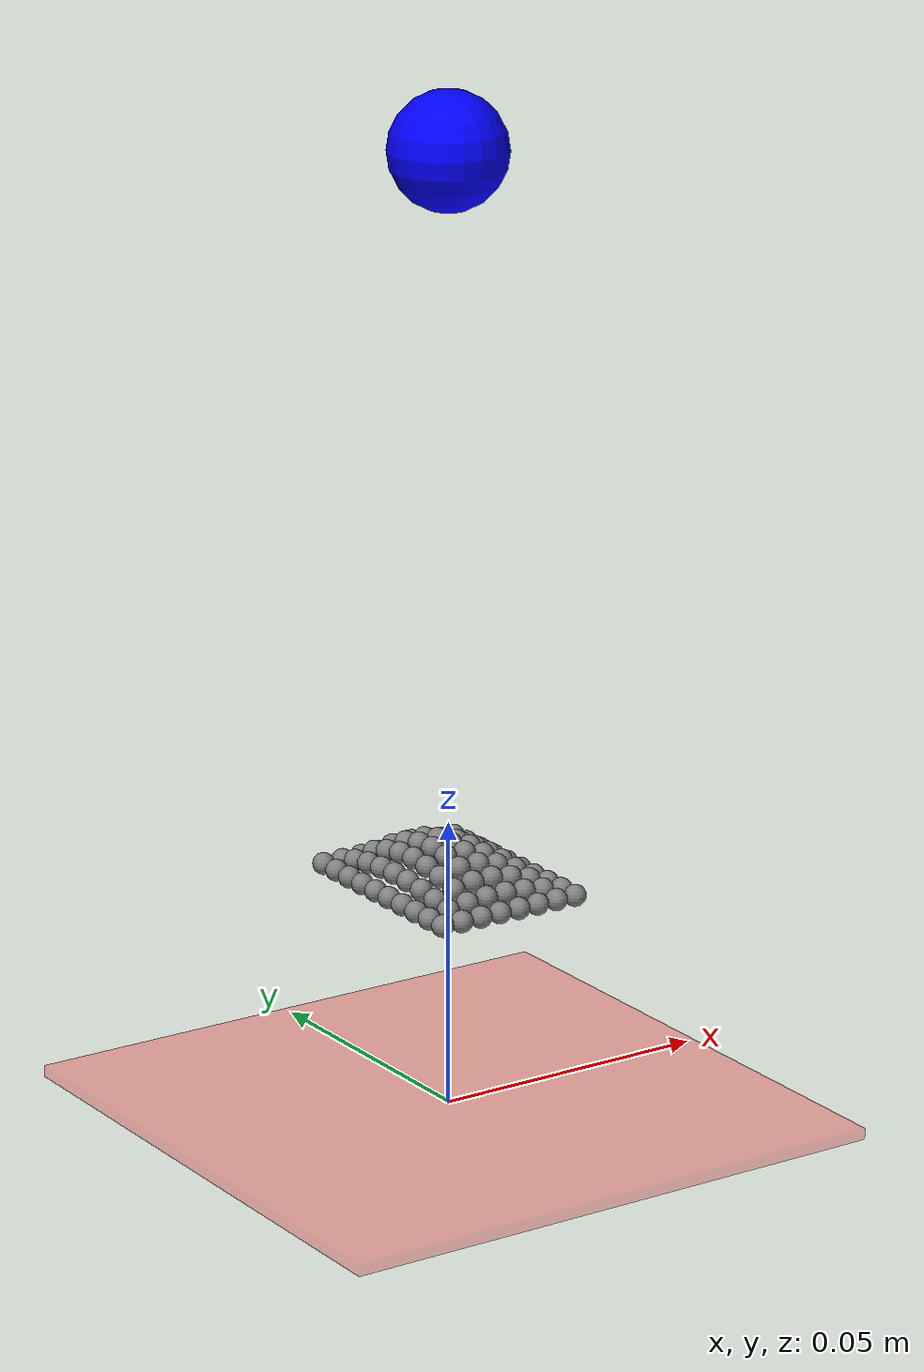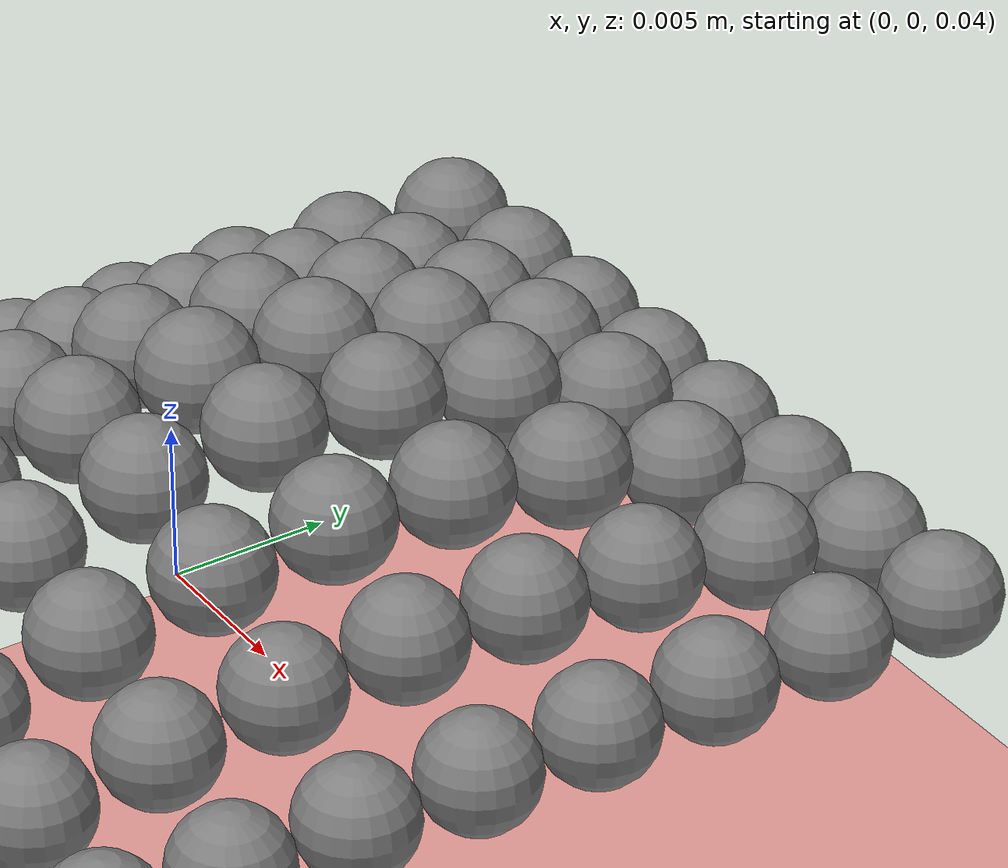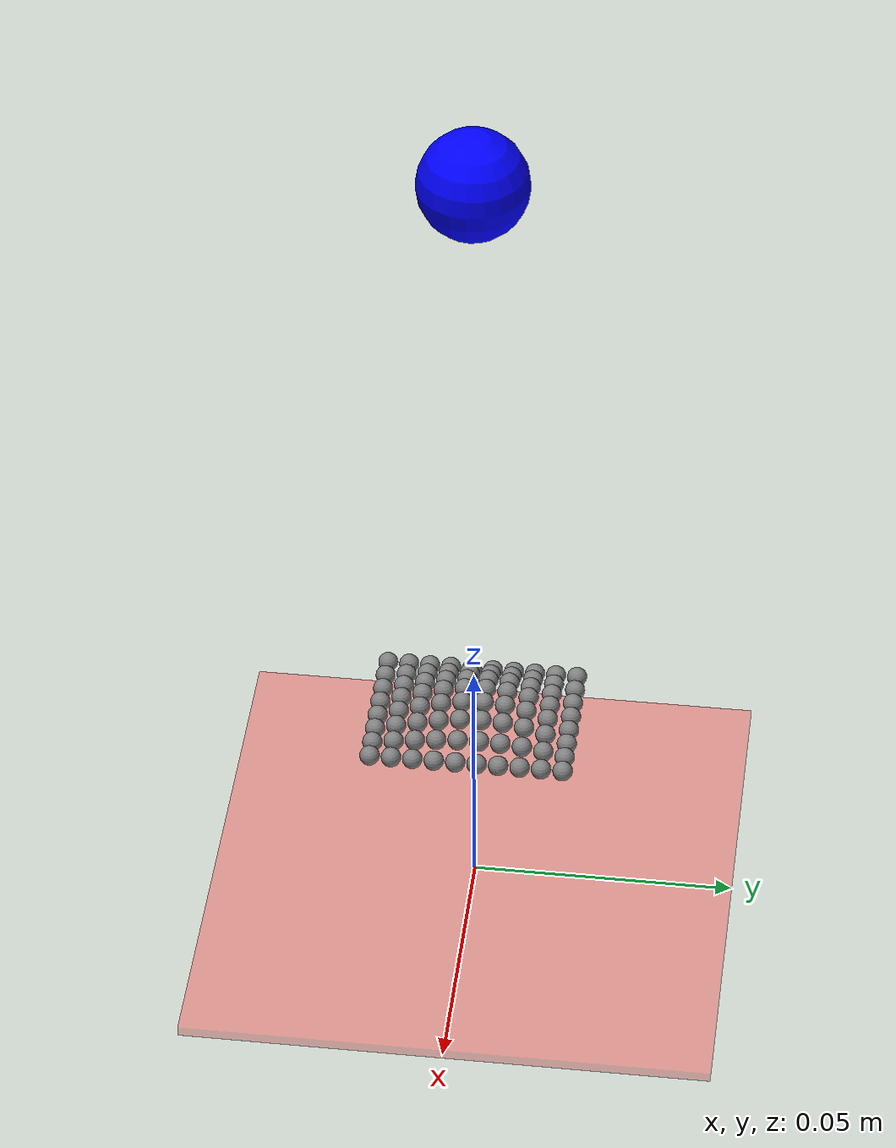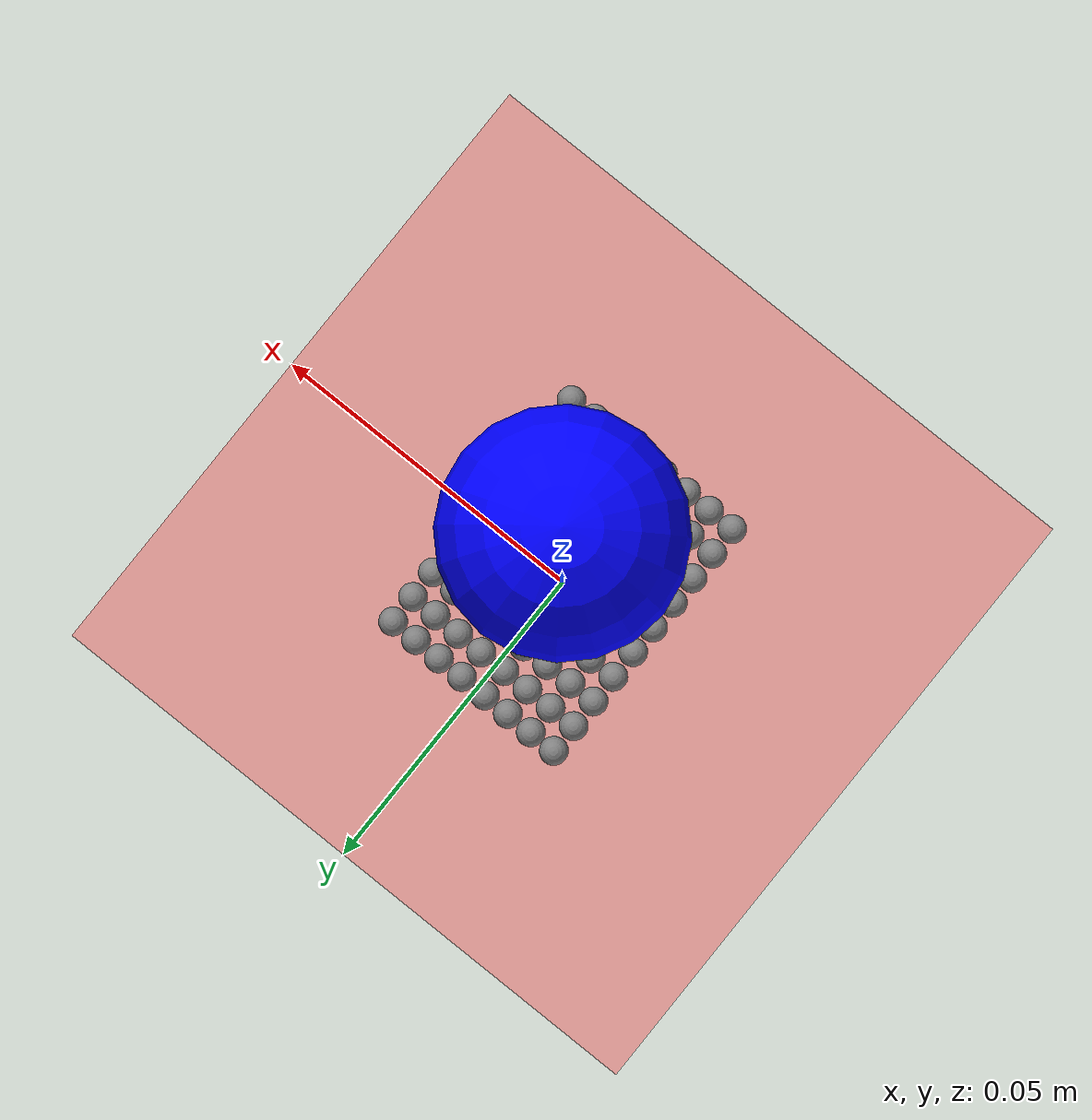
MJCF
<mujoco model="MuJoCo Model">
  <compiler angle="radian"/>

  <option timestep="0.0001" integrator="implicitfast"/>

  <default>
    <joint armature="0.01" frictionloss="0.01"/>
    <geom conaffinity="2" condim="4" friction="0.9 0.2 0.2" solref="0.001"/>

    <equality solref="1e-06 30"/>
    <general ctrllimited="true" biastype="affine" gainprm="1000000" biasprm="0 -1000000"/>
  </default>

  <asset>
    <texture type="skybox" builtin="gradient" rgb1="1 1 1" rgb2="1 1 1" width="265" height="1590"/>
    <texture type="2d" name="grid" builtin="checker" rgb1="0.1 0.2 0.3" rgb2="0.2 0.3 0.4" width="300" height="300"/>
    <material name="grid" texture="grid" texrepeat="10 10" reflectance="0.2"/>
  </asset>

  <worldbody>
    <light pos="0 0 10" dir="0 0 -1"/>
    <body name="base_plate">
      <geom name="plate_geom" size="0.05 0.05 0.001" type="box" rgba="1 0 0 0.3"/>
      <body name="pin_0_0">
        <joint name="pin_0_0_joint" pos="0 0 0" axis="0 0 1" type="slide" stiffness="5" range="-0.04 0" damping="0.1"/>
        <geom name="pin_0_0_geom" size="0.001875" pos="-0.013125 -0.018125 0.04" contype="2" conaffinity="1"/>
        <site name="pin_0_0_site" pos="-0.013125 -0.018125 0.04" size="0.000375" rgba="1 0 0 1"/>
      </body>
      <body name="pin_0_1">
        <joint name="pin_0_1_joint" pos="0 0 0" axis="0 0 1" type="slide" stiffness="5" range="-0.04 0" damping="0.1"/>
        <geom name="pin_0_1_geom" size="0.001875" pos="-0.009375 -0.018125 0.04" contype="2" conaffinity="1"/>
        <site name="pin_0_1_site" pos="-0.009375 -0.018125 0.04" size="0.000375" rgba="1 0 0 1"/>
      </body>
      <body name="pin_0_2">
        <joint name="pin_0_2_joint" pos="0 0 0" axis="0 0 1" type="slide" stiffness="5" range="-0.04 0" damping="0.1"/>
        <geom name="pin_0_2_geom" size="0.001875" pos="-0.005625 -0.018125 0.04" contype="2" conaffinity="1"/>
        <site name="pin_0_2_site" pos="-0.005625 -0.018125 0.04" size="0.000375" rgba="1 0 0 1"/>
      </body>
      <body name="pin_0_3">
        <joint name="pin_0_3_joint" pos="0 0 0" axis="0 0 1" type="slide" stiffness="5" range="-0.04 0" damping="0.1"/>
        <geom name="pin_0_3_geom" size="0.001875" pos="-0.001875 -0.018125 0.04" contype="2" conaffinity="1"/>
        <site name="pin_0_3_site" pos="-0.001875 -0.018125 0.04" size="0.000375" rgba="1 0 0 1"/>
      </body>
      <body name="pin_0_4">
        <joint name="pin_0_4_joint" pos="0 0 0" axis="0 0 1" type="slide" stiffness="5" range="-0.04 0" damping="0.1"/>
        <geom name="pin_0_4_geom" size="0.001875" pos="0.001875 -0.018125 0.04" contype="2" conaffinity="1"/>
        <site name="pin_0_4_site" pos="0.001875 -0.018125 0.04" size="0.000375" rgba="1 0 0 1"/>
      </body>
      <body name="pin_0_5">
        <joint name="pin_0_5_joint" pos="0 0 0" axis="0 0 1" type="slide" stiffness="5" range="-0.04 0" damping="0.1"/>
        <geom name="pin_0_5_geom" size="0.001875" pos="0.005625 -0.018125 0.04" contype="2" conaffinity="1"/>
        <site name="pin_0_5_site" pos="0.005625 -0.018125 0.04" size="0.000375" rgba="1 0 0 1"/>
      </body>
      <body name="pin_0_6">
        <joint name="pin_0_6_joint" pos="0 0 0" axis="0 0 1" type="slide" stiffness="5" range="-0.04 0" damping="0.1"/>
        <geom name="pin_0_6_geom" size="0.001875" pos="0.009375 -0.018125 0.04" contype="2" conaffinity="1"/>
        <site name="pin_0_6_site" pos="0.009375 -0.018125 0.04" size="0.000375" rgba="1 0 0 1"/>
      </body>
      <body name="pin_0_7">
        <joint name="pin_0_7_joint" pos="0 0 0" axis="0 0 1" type="slide" stiffness="5" range="-0.04 0" damping="0.1"/>
        <geom name="pin_0_7_geom" size="0.001875" pos="0.013125 -0.018125 0.04" contype="2" conaffinity="1"/>
        <site name="pin_0_7_site" pos="0.013125 -0.018125 0.04" size="0.000375" rgba="1 0 0 1"/>
      </body>
      <body name="pin_1_0">
        <joint name="pin_1_0_joint" pos="0 0 0" axis="0 0 1" type="slide" stiffness="5" range="-0.04 0" damping="0.1"/>
        <geom name="pin_1_0_geom" size="0.001875" pos="-0.013125 -0.0140972 0.04" contype="2" conaffinity="1"/>
        <site name="pin_1_0_site" pos="-0.013125 -0.0140972 0.04" size="0.000375" rgba="1 0 0 1"/>
      </body>
      <body name="pin_1_1">
        <joint name="pin_1_1_joint" pos="0 0 0" axis="0 0 1" type="slide" stiffness="5" range="-0.0406874 0" damping="0.1"/>
        <geom name="pin_1_1_geom" size="0.001875" pos="-0.009375 -0.0140972 0.0406874" contype="2" conaffinity="1"/>
        <site name="pin_1_1_site" pos="-0.009375 -0.0140972 0.0406874" size="0.000375" rgba="1 0 0 1"/>
      </body>
      <body name="pin_1_2">
        <joint name="pin_1_2_joint" pos="0 0 0" axis="0 0 1" type="slide" stiffness="5" range="-0.0412272 0" damping="0.1"/>
        <geom name="pin_1_2_geom" size="0.001875" pos="-0.005625 -0.0140972 0.0412272" contype="2" conaffinity="1"/>
        <site name="pin_1_2_site" pos="-0.005625 -0.0140972 0.0412272" size="0.000375" rgba="1 0 0 1"/>
      </body>
      <body name="pin_1_3">
        <joint name="pin_1_3_joint" pos="0 0 0" axis="0 0 1" type="slide" stiffness="5" range="-0.0415216 0" damping="0.1"/>
        <geom name="pin_1_3_geom" size="0.001875" pos="-0.001875 -0.0140972 0.0415216" contype="2" conaffinity="1"/>
        <site name="pin_1_3_site" pos="-0.001875 -0.0140972 0.0415216" size="0.000375" rgba="1 0 0 1"/>
      </body>
      <body name="pin_1_4">
        <joint name="pin_1_4_joint" pos="0 0 0" axis="0 0 1" type="slide" stiffness="5" range="-0.0415216 0" damping="0.1"/>
        <geom name="pin_1_4_geom" size="0.001875" pos="0.001875 -0.0140972 0.0415216" contype="2" conaffinity="1"/>
        <site name="pin_1_4_site" pos="0.001875 -0.0140972 0.0415216" size="0.000375" rgba="1 0 0 1"/>
      </body>
      <body name="pin_1_5">
        <joint name="pin_1_5_joint" pos="0 0 0" axis="0 0 1" type="slide" stiffness="5" range="-0.0412272 0" damping="0.1"/>
        <geom name="pin_1_5_geom" size="0.001875" pos="0.005625 -0.0140972 0.0412272" contype="2" conaffinity="1"/>
        <site name="pin_1_5_site" pos="0.005625 -0.0140972 0.0412272" size="0.000375" rgba="1 0 0 1"/>
      </body>
      <body name="pin_1_6">
        <joint name="pin_1_6_joint" pos="0 0 0" axis="0 0 1" type="slide" stiffness="5" range="-0.0406874 0" damping="0.1"/>
        <geom name="pin_1_6_geom" size="0.001875" pos="0.009375 -0.0140972 0.0406874" contype="2" conaffinity="1"/>
        <site name="pin_1_6_site" pos="0.009375 -0.0140972 0.0406874" size="0.000375" rgba="1 0 0 1"/>
      </body>
      <body name="pin_1_7">
        <joint name="pin_1_7_joint" pos="0 0 0" axis="0 0 1" type="slide" stiffness="5" range="-0.04 0" damping="0.1"/>
        <geom name="pin_1_7_geom" size="0.001875" pos="0.013125 -0.0140972 0.04" contype="2" conaffinity="1"/>
        <site name="pin_1_7_site" pos="0.013125 -0.0140972 0.04" size="0.000375" rgba="1 0 0 1"/>
      </body>
      <body name="pin_2_0">
        <joint name="pin_2_0_joint" pos="0 0 0" axis="0 0 1" type="slide" stiffness="5" range="-0.04 0" damping="0.1"/>
        <geom name="pin_2_0_geom" size="0.001875" pos="-0.013125 -0.0100694 0.04" contype="2" conaffinity="1"/>
        <site name="pin_2_0_site" pos="-0.013125 -0.0100694 0.04" size="0.000375" rgba="1 0 0 1"/>
      </body>
      <body name="pin_2_1">
        <joint name="pin_2_1_joint" pos="0 0 0" axis="0 0 1" type="slide" stiffness="5" range="-0.0413193 0" damping="0.1"/>
        <geom name="pin_2_1_geom" size="0.001875" pos="-0.009375 -0.0100694 0.0413193" contype="2" conaffinity="1"/>
        <site name="pin_2_1_site" pos="-0.009375 -0.0100694 0.0413193" size="0.000375" rgba="1 0 0 1"/>
      </body>
      <body name="pin_2_2">
        <joint name="pin_2_2_joint" pos="0 0 0" axis="0 0 1" type="slide" stiffness="5" range="-0.0424014 0" damping="0.1"/>
        <geom name="pin_2_2_geom" size="0.001875" pos="-0.005625 -0.0100694 0.0424014" contype="2" conaffinity="1"/>
        <site name="pin_2_2_site" pos="-0.005625 -0.0100694 0.0424014" size="0.000375" rgba="1 0 0 1"/>
      </body>
      <body name="pin_2_3">
        <joint name="pin_2_3_joint" pos="0 0 0" axis="0 0 1" type="slide" stiffness="5" range="-0.0430032 0" damping="0.1"/>
        <geom name="pin_2_3_geom" size="0.001875" pos="-0.001875 -0.0100694 0.0430032" contype="2" conaffinity="1"/>
        <site name="pin_2_3_site" pos="-0.001875 -0.0100694 0.0430032" size="0.000375" rgba="1 0 0 1"/>
      </body>
      <body name="pin_2_4">
        <joint name="pin_2_4_joint" pos="0 0 0" axis="0 0 1" type="slide" stiffness="5" range="-0.0430032 0" damping="0.1"/>
        <geom name="pin_2_4_geom" size="0.001875" pos="0.001875 -0.0100694 0.0430032" contype="2" conaffinity="1"/>
        <site name="pin_2_4_site" pos="0.001875 -0.0100694 0.0430032" size="0.000375" rgba="1 0 0 1"/>
      </body>
      <body name="pin_2_5">
        <joint name="pin_2_5_joint" pos="0 0 0" axis="0 0 1" type="slide" stiffness="5" range="-0.0424014 0" damping="0.1"/>
        <geom name="pin_2_5_geom" size="0.001875" pos="0.005625 -0.0100694 0.0424014" contype="2" conaffinity="1"/>
        <site name="pin_2_5_site" pos="0.005625 -0.0100694 0.0424014" size="0.000375" rgba="1 0 0 1"/>
      </body>
      <body name="pin_2_6">
        <joint name="pin_2_6_joint" pos="0 0 0" axis="0 0 1" type="slide" stiffness="5" range="-0.0413193 0" damping="0.1"/>
        <geom name="pin_2_6_geom" size="0.001875" pos="0.009375 -0.0100694 0.0413193" contype="2" conaffinity="1"/>
        <site name="pin_2_6_site" pos="0.009375 -0.0100694 0.0413193" size="0.000375" rgba="1 0 0 1"/>
      </body>
      <body name="pin_2_7">
        <joint name="pin_2_7_joint" pos="0 0 0" axis="0 0 1" type="slide" stiffness="5" range="-0.04 0" damping="0.1"/>
        <geom name="pin_2_7_geom" size="0.001875" pos="0.013125 -0.0100694 0.04" contype="2" conaffinity="1"/>
        <site name="pin_2_7_site" pos="0.013125 -0.0100694 0.04" size="0.000375" rgba="1 0 0 1"/>
      </body>
      <body name="pin_3_0">
        <joint name="pin_3_0_joint" pos="0 0 0" axis="0 0 1" type="slide" stiffness="5" range="-0.04 0" damping="0.1"/>
        <geom name="pin_3_0_geom" size="0.001875" pos="-0.013125 -0.00604167 0.04" contype="2" conaffinity="1"/>
        <site name="pin_3_0_site" pos="-0.013125 -0.00604167 0.04" size="0.000375" rgba="1 0 0 1"/>
      </body>
      <body name="pin_3_1">
        <joint name="pin_3_1_joint" pos="0 0 0" axis="0 0 1" type="slide" stiffness="5" range="-0.0418353 0" damping="0.1"/>
        <geom name="pin_3_1_geom" size="0.001875" pos="-0.009375 -0.00604167 0.0418353" contype="2" conaffinity="1"/>
        <site name="pin_3_1_site" pos="-0.009375 -0.00604167 0.0418353" size="0.000375" rgba="1 0 0 1"/>
      </body>
      <body name="pin_3_2">
        <joint name="pin_3_2_joint" pos="0 0 0" axis="0 0 1" type="slide" stiffness="5" range="-0.043378 0" damping="0.1"/>
        <geom name="pin_3_2_geom" size="0.001875" pos="-0.005625 -0.00604167 0.043378" contype="2" conaffinity="1"/>
        <site name="pin_3_2_site" pos="-0.005625 -0.00604167 0.043378" size="0.000375" rgba="1 0 0 1"/>
      </body>
      <body name="pin_3_3">
        <joint name="pin_3_3_joint" pos="0 0 0" axis="0 0 1" type="slide" stiffness="5" range="-0.0442451 0" damping="0.1"/>
        <geom name="pin_3_3_geom" size="0.001875" pos="-0.001875 -0.00604167 0.0442451" contype="2" conaffinity="1"/>
        <site name="pin_3_3_site" pos="-0.001875 -0.00604167 0.0442451" size="0.000375" rgba="1 0 0 1"/>
      </body>
      <body name="pin_3_4">
        <joint name="pin_3_4_joint" pos="0 0 0" axis="0 0 1" type="slide" stiffness="5" range="-0.0442451 0" damping="0.1"/>
        <geom name="pin_3_4_geom" size="0.001875" pos="0.001875 -0.00604167 0.0442451" contype="2" conaffinity="1"/>
        <site name="pin_3_4_site" pos="0.001875 -0.00604167 0.0442451" size="0.000375" rgba="1 0 0 1"/>
      </body>
      <body name="pin_3_5">
        <joint name="pin_3_5_joint" pos="0 0 0" axis="0 0 1" type="slide" stiffness="5" range="-0.043378 0" damping="0.1"/>
        <geom name="pin_3_5_geom" size="0.001875" pos="0.005625 -0.00604167 0.043378" contype="2" conaffinity="1"/>
        <site name="pin_3_5_site" pos="0.005625 -0.00604167 0.043378" size="0.000375" rgba="1 0 0 1"/>
      </body>
      <body name="pin_3_6">
        <joint name="pin_3_6_joint" pos="0 0 0" axis="0 0 1" type="slide" stiffness="5" range="-0.0418353 0" damping="0.1"/>
        <geom name="pin_3_6_geom" size="0.001875" pos="0.009375 -0.00604167 0.0418353" contype="2" conaffinity="1"/>
        <site name="pin_3_6_site" pos="0.009375 -0.00604167 0.0418353" size="0.000375" rgba="1 0 0 1"/>
      </body>
      <body name="pin_3_7">
        <joint name="pin_3_7_joint" pos="0 0 0" axis="0 0 1" type="slide" stiffness="5" range="-0.04 0" damping="0.1"/>
        <geom name="pin_3_7_geom" size="0.001875" pos="0.013125 -0.00604167 0.04" contype="2" conaffinity="1"/>
        <site name="pin_3_7_site" pos="0.013125 -0.00604167 0.04" size="0.000375" rgba="1 0 0 1"/>
      </body>
      <body name="pin_4_0">
        <joint name="pin_4_0_joint" pos="0 0 0" axis="0 0 1" type="slide" stiffness="5" range="-0.04 0" damping="0.1"/>
        <geom name="pin_4_0_geom" size="0.001875" pos="-0.013125 -0.00201389 0.04" contype="2" conaffinity="1"/>
        <site name="pin_4_0_site" pos="-0.013125 -0.00201389 0.04" size="0.000375" rgba="1 0 0 1"/>
      </body>
      <body name="pin_4_1">
        <joint name="pin_4_1_joint" pos="0 0 0" axis="0 0 1" type="slide" stiffness="5" range="-0.0421817 0" damping="0.1"/>
        <geom name="pin_4_1_geom" size="0.001875" pos="-0.009375 -0.00201389 0.0421817" contype="2" conaffinity="1"/>
        <site name="pin_4_1_site" pos="-0.009375 -0.00201389 0.0421817" size="0.000375" rgba="1 0 0 1"/>
      </body>
      <body name="pin_4_2">
        <joint name="pin_4_2_joint" pos="0 0 0" axis="0 0 1" type="slide" stiffness="5" range="-0.0440363 0" damping="0.1"/>
        <geom name="pin_4_2_geom" size="0.001875" pos="-0.005625 -0.00201389 0.0440363" contype="2" conaffinity="1"/>
        <site name="pin_4_2_site" pos="-0.005625 -0.00201389 0.0440363" size="0.000375" rgba="1 0 0 1"/>
      </body>
      <body name="pin_4_3">
        <joint name="pin_4_3_joint" pos="0 0 0" axis="0 0 1" type="slide" stiffness="5" range="-0.0450837 0" damping="0.1"/>
        <geom name="pin_4_3_geom" size="0.001875" pos="-0.001875 -0.00201389 0.0450837" contype="2" conaffinity="1"/>
        <site name="pin_4_3_site" pos="-0.001875 -0.00201389 0.0450837" size="0.000375" rgba="1 0 0 1"/>
      </body>
      <body name="pin_4_4">
        <joint name="pin_4_4_joint" pos="0 0 0" axis="0 0 1" type="slide" stiffness="5" range="-0.0450837 0" damping="0.1"/>
        <geom name="pin_4_4_geom" size="0.001875" pos="0.001875 -0.00201389 0.0450837" contype="2" conaffinity="1"/>
        <site name="pin_4_4_site" pos="0.001875 -0.00201389 0.0450837" size="0.000375" rgba="1 0 0 1"/>
      </body>
      <body name="pin_4_5">
        <joint name="pin_4_5_joint" pos="0 0 0" axis="0 0 1" type="slide" stiffness="5" range="-0.0440363 0" damping="0.1"/>
        <geom name="pin_4_5_geom" size="0.001875" pos="0.005625 -0.00201389 0.0440363" contype="2" conaffinity="1"/>
        <site name="pin_4_5_site" pos="0.005625 -0.00201389 0.0440363" size="0.000375" rgba="1 0 0 1"/>
      </body>
      <body name="pin_4_6">
        <joint name="pin_4_6_joint" pos="0 0 0" axis="0 0 1" type="slide" stiffness="5" range="-0.0421817 0" damping="0.1"/>
        <geom name="pin_4_6_geom" size="0.001875" pos="0.009375 -0.00201389 0.0421817" contype="2" conaffinity="1"/>
        <site name="pin_4_6_site" pos="0.009375 -0.00201389 0.0421817" size="0.000375" rgba="1 0 0 1"/>
      </body>
      <body name="pin_4_7">
        <joint name="pin_4_7_joint" pos="0 0 0" axis="0 0 1" type="slide" stiffness="5" range="-0.04 0" damping="0.1"/>
        <geom name="pin_4_7_geom" size="0.001875" pos="0.013125 -0.00201389 0.04" contype="2" conaffinity="1"/>
        <site name="pin_4_7_site" pos="0.013125 -0.00201389 0.04" size="0.000375" rgba="1 0 0 1"/>
      </body>
      <body name="pin_5_0">
        <joint name="pin_5_0_joint" pos="0 0 0" axis="0 0 1" type="slide" stiffness="5" range="-0.04 0" damping="0.1"/>
        <geom name="pin_5_0_geom" size="0.001875" pos="-0.013125 0.00201389 0.04" contype="2" conaffinity="1"/>
        <site name="pin_5_0_site" pos="-0.013125 0.00201389 0.04" size="0.000375" rgba="1 0 0 1"/>
      </body>
      <body name="pin_5_1">
        <joint name="pin_5_1_joint" pos="0 0 0" axis="0 0 1" type="slide" stiffness="5" range="-0.0423122 0" damping="0.1"/>
        <geom name="pin_5_1_geom" size="0.001875" pos="-0.009375 0.00201389 0.0423122" contype="2" conaffinity="1"/>
        <site name="pin_5_1_site" pos="-0.009375 0.00201389 0.0423122" size="0.000375" rgba="1 0 0 1"/>
      </body>
      <body name="pin_5_2">
        <joint name="pin_5_2_joint" pos="0 0 0" axis="0 0 1" type="slide" stiffness="5" range="-0.0442795 0" damping="0.1"/>
        <geom name="pin_5_2_geom" size="0.001875" pos="-0.005625 0.00201389 0.0442795" contype="2" conaffinity="1"/>
        <site name="pin_5_2_site" pos="-0.005625 0.00201389 0.0442795" size="0.000375" rgba="1 0 0 1"/>
      </body>
      <body name="pin_5_3">
        <joint name="pin_5_3_joint" pos="0 0 0" axis="0 0 1" type="slide" stiffness="5" range="-0.0453908 0" damping="0.1"/>
        <geom name="pin_5_3_geom" size="0.001875" pos="-0.001875 0.00201389 0.0453908" contype="2" conaffinity="1"/>
        <site name="pin_5_3_site" pos="-0.001875 0.00201389 0.0453908" size="0.000375" rgba="1 0 0 1"/>
      </body>
      <body name="pin_5_4">
        <joint name="pin_5_4_joint" pos="0 0 0" axis="0 0 1" type="slide" stiffness="5" range="-0.0453908 0" damping="0.1"/>
        <geom name="pin_5_4_geom" size="0.001875" pos="0.001875 0.00201389 0.0453908" contype="2" conaffinity="1"/>
        <site name="pin_5_4_site" pos="0.001875 0.00201389 0.0453908" size="0.000375" rgba="1 0 0 1"/>
      </body>
      <body name="pin_5_5">
        <joint name="pin_5_5_joint" pos="0 0 0" axis="0 0 1" type="slide" stiffness="5" range="-0.0442795 0" damping="0.1"/>
        <geom name="pin_5_5_geom" size="0.001875" pos="0.005625 0.00201389 0.0442795" contype="2" conaffinity="1"/>
        <site name="pin_5_5_site" pos="0.005625 0.00201389 0.0442795" size="0.000375" rgba="1 0 0 1"/>
      </body>
      <body name="pin_5_6">
        <joint name="pin_5_6_joint" pos="0 0 0" axis="0 0 1" type="slide" stiffness="5" range="-0.0423122 0" damping="0.1"/>
        <geom name="pin_5_6_geom" size="0.001875" pos="0.009375 0.00201389 0.0423122" contype="2" conaffinity="1"/>
        <site name="pin_5_6_site" pos="0.009375 0.00201389 0.0423122" size="0.000375" rgba="1 0 0 1"/>
      </body>
      <body name="pin_5_7">
        <joint name="pin_5_7_joint" pos="0 0 0" axis="0 0 1" type="slide" stiffness="5" range="-0.04 0" damping="0.1"/>
        <geom name="pin_5_7_geom" size="0.001875" pos="0.013125 0.00201389 0.04" contype="2" conaffinity="1"/>
        <site name="pin_5_7_site" pos="0.013125 0.00201389 0.04" size="0.000375" rgba="1 0 0 1"/>
      </body>
      <body name="pin_6_0">
        <joint name="pin_6_0_joint" pos="0 0 0" axis="0 0 1" type="slide" stiffness="5" range="-0.04 0" damping="0.1"/>
        <geom name="pin_6_0_geom" size="0.001875" pos="-0.013125 0.00604167 0.04" contype="2" conaffinity="1"/>
        <site name="pin_6_0_site" pos="-0.013125 0.00604167 0.04" size="0.000375" rgba="1 0 0 1"/>
      </body>
      <body name="pin_6_1">
        <joint name="pin_6_1_joint" pos="0 0 0" axis="0 0 1" type="slide" stiffness="5" range="-0.0421877 0" damping="0.1"/>
        <geom name="pin_6_1_geom" size="0.001875" pos="-0.009375 0.00604167 0.0421877" contype="2" conaffinity="1"/>
        <site name="pin_6_1_site" pos="-0.009375 0.00604167 0.0421877" size="0.000375" rgba="1 0 0 1"/>
      </body>
      <body name="pin_6_2">
        <joint name="pin_6_2_joint" pos="0 0 0" axis="0 0 1" type="slide" stiffness="5" range="-0.0440345 0" damping="0.1"/>
        <geom name="pin_6_2_geom" size="0.001875" pos="-0.005625 0.00604167 0.0440345" contype="2" conaffinity="1"/>
        <site name="pin_6_2_site" pos="-0.005625 0.00604167 0.0440345" size="0.000375" rgba="1 0 0 1"/>
      </body>
      <body name="pin_6_3">
        <joint name="pin_6_3_joint" pos="0 0 0" axis="0 0 1" type="slide" stiffness="5" range="-0.0450744 0" damping="0.1"/>
        <geom name="pin_6_3_geom" size="0.001875" pos="-0.001875 0.00604167 0.0450744" contype="2" conaffinity="1"/>
        <site name="pin_6_3_site" pos="-0.001875 0.00604167 0.0450744" size="0.000375" rgba="1 0 0 1"/>
      </body>
      <body name="pin_6_4">
        <joint name="pin_6_4_joint" pos="0 0 0" axis="0 0 1" type="slide" stiffness="5" range="-0.0450744 0" damping="0.1"/>
        <geom name="pin_6_4_geom" size="0.001875" pos="0.001875 0.00604167 0.0450744" contype="2" conaffinity="1"/>
        <site name="pin_6_4_site" pos="0.001875 0.00604167 0.0450744" size="0.000375" rgba="1 0 0 1"/>
      </body>
      <body name="pin_6_5">
        <joint name="pin_6_5_joint" pos="0 0 0" axis="0 0 1" type="slide" stiffness="5" range="-0.0440345 0" damping="0.1"/>
        <geom name="pin_6_5_geom" size="0.001875" pos="0.005625 0.00604167 0.0440345" contype="2" conaffinity="1"/>
        <site name="pin_6_5_site" pos="0.005625 0.00604167 0.0440345" size="0.000375" rgba="1 0 0 1"/>
      </body>
      <body name="pin_6_6">
        <joint name="pin_6_6_joint" pos="0 0 0" axis="0 0 1" type="slide" stiffness="5" range="-0.0421877 0" damping="0.1"/>
        <geom name="pin_6_6_geom" size="0.001875" pos="0.009375 0.00604167 0.0421877" contype="2" conaffinity="1"/>
        <site name="pin_6_6_site" pos="0.009375 0.00604167 0.0421877" size="0.000375" rgba="1 0 0 1"/>
      </body>
      <body name="pin_6_7">
        <joint name="pin_6_7_joint" pos="0 0 0" axis="0 0 1" type="slide" stiffness="5" range="-0.04 0" damping="0.1"/>
        <geom name="pin_6_7_geom" size="0.001875" pos="0.013125 0.00604167 0.04" contype="2" conaffinity="1"/>
        <site name="pin_6_7_site" pos="0.013125 0.00604167 0.04" size="0.000375" rgba="1 0 0 1"/>
      </body>
      <body name="pin_7_0">
        <joint name="pin_7_0_joint" pos="0 0 0" axis="0 0 1" type="slide" stiffness="5" range="-0.04 0" damping="0.1"/>
        <geom name="pin_7_0_geom" size="0.001875" pos="-0.013125 0.0100694 0.04" contype="2" conaffinity="1"/>
        <site name="pin_7_0_site" pos="-0.013125 0.0100694 0.04" size="0.000375" rgba="1 0 0 1"/>
      </body>
      <body name="pin_7_1">
        <joint name="pin_7_1_joint" pos="0 0 0" axis="0 0 1" type="slide" stiffness="5" range="-0.0417762 0" damping="0.1"/>
        <geom name="pin_7_1_geom" size="0.001875" pos="-0.009375 0.0100694 0.0417762" contype="2" conaffinity="1"/>
        <site name="pin_7_1_site" pos="-0.009375 0.0100694 0.0417762" size="0.000375" rgba="1 0 0 1"/>
      </body>
      <body name="pin_7_2">
        <joint name="pin_7_2_joint" pos="0 0 0" axis="0 0 1" type="slide" stiffness="5" range="-0.0432524 0" damping="0.1"/>
        <geom name="pin_7_2_geom" size="0.001875" pos="-0.005625 0.0100694 0.0432524" contype="2" conaffinity="1"/>
        <site name="pin_7_2_site" pos="-0.005625 0.0100694 0.0432524" size="0.000375" rgba="1 0 0 1"/>
      </body>
      <body name="pin_7_3">
        <joint name="pin_7_3_joint" pos="0 0 0" axis="0 0 1" type="slide" stiffness="5" range="-0.0440782 0" damping="0.1"/>
        <geom name="pin_7_3_geom" size="0.001875" pos="-0.001875 0.0100694 0.0440782" contype="2" conaffinity="1"/>
        <site name="pin_7_3_site" pos="-0.001875 0.0100694 0.0440782" size="0.000375" rgba="1 0 0 1"/>
      </body>
      <body name="pin_7_4">
        <joint name="pin_7_4_joint" pos="0 0 0" axis="0 0 1" type="slide" stiffness="5" range="-0.0440782 0" damping="0.1"/>
        <geom name="pin_7_4_geom" size="0.001875" pos="0.001875 0.0100694 0.0440782" contype="2" conaffinity="1"/>
        <site name="pin_7_4_site" pos="0.001875 0.0100694 0.0440782" size="0.000375" rgba="1 0 0 1"/>
      </body>
      <body name="pin_7_5">
        <joint name="pin_7_5_joint" pos="0 0 0" axis="0 0 1" type="slide" stiffness="5" range="-0.0432524 0" damping="0.1"/>
        <geom name="pin_7_5_geom" size="0.001875" pos="0.005625 0.0100694 0.0432524" contype="2" conaffinity="1"/>
        <site name="pin_7_5_site" pos="0.005625 0.0100694 0.0432524" size="0.000375" rgba="1 0 0 1"/>
      </body>
      <body name="pin_7_6">
        <joint name="pin_7_6_joint" pos="0 0 0" axis="0 0 1" type="slide" stiffness="5" range="-0.0417762 0" damping="0.1"/>
        <geom name="pin_7_6_geom" size="0.001875" pos="0.009375 0.0100694 0.0417762" contype="2" conaffinity="1"/>
        <site name="pin_7_6_site" pos="0.009375 0.0100694 0.0417762" size="0.000375" rgba="1 0 0 1"/>
      </body>
      <body name="pin_7_7">
        <joint name="pin_7_7_joint" pos="0 0 0" axis="0 0 1" type="slide" stiffness="5" range="-0.04 0" damping="0.1"/>
        <geom name="pin_7_7_geom" size="0.001875" pos="0.013125 0.0100694 0.04" contype="2" conaffinity="1"/>
        <site name="pin_7_7_site" pos="0.013125 0.0100694 0.04" size="0.000375" rgba="1 0 0 1"/>
      </body>
      <body name="pin_8_0">
        <joint name="pin_8_0_joint" pos="0 0 0" axis="0 0 1" type="slide" stiffness="5" range="-0.04 0" damping="0.1"/>
        <geom name="pin_8_0_geom" size="0.001875" pos="-0.013125 0.0140972 0.04" contype="2" conaffinity="1"/>
        <site name="pin_8_0_site" pos="-0.013125 0.0140972 0.04" size="0.000375" rgba="1 0 0 1"/>
      </body>
      <body name="pin_8_1">
        <joint name="pin_8_1_joint" pos="0 0 0" axis="0 0 1" type="slide" stiffness="5" range="-0.0410529 0" damping="0.1"/>
        <geom name="pin_8_1_geom" size="0.001875" pos="-0.009375 0.0140972 0.0410529" contype="2" conaffinity="1"/>
        <site name="pin_8_1_site" pos="-0.009375 0.0140972 0.0410529" size="0.000375" rgba="1 0 0 1"/>
      </body>
      <body name="pin_8_2">
        <joint name="pin_8_2_joint" pos="0 0 0" axis="0 0 1" type="slide" stiffness="5" range="-0.041908 0" damping="0.1"/>
        <geom name="pin_8_2_geom" size="0.001875" pos="-0.005625 0.0140972 0.041908" contype="2" conaffinity="1"/>
        <site name="pin_8_2_site" pos="-0.005625 0.0140972 0.041908" size="0.000375" rgba="1 0 0 1"/>
      </body>
      <body name="pin_8_3">
        <joint name="pin_8_3_joint" pos="0 0 0" axis="0 0 1" type="slide" stiffness="5" range="-0.0423816 0" damping="0.1"/>
        <geom name="pin_8_3_geom" size="0.001875" pos="-0.001875 0.0140972 0.0423816" contype="2" conaffinity="1"/>
        <site name="pin_8_3_site" pos="-0.001875 0.0140972 0.0423816" size="0.000375" rgba="1 0 0 1"/>
      </body>
      <body name="pin_8_4">
        <joint name="pin_8_4_joint" pos="0 0 0" axis="0 0 1" type="slide" stiffness="5" range="-0.0423816 0" damping="0.1"/>
        <geom name="pin_8_4_geom" size="0.001875" pos="0.001875 0.0140972 0.0423816" contype="2" conaffinity="1"/>
        <site name="pin_8_4_site" pos="0.001875 0.0140972 0.0423816" size="0.000375" rgba="1 0 0 1"/>
      </body>
      <body name="pin_8_5">
        <joint name="pin_8_5_joint" pos="0 0 0" axis="0 0 1" type="slide" stiffness="5" range="-0.041908 0" damping="0.1"/>
        <geom name="pin_8_5_geom" size="0.001875" pos="0.005625 0.0140972 0.041908" contype="2" conaffinity="1"/>
        <site name="pin_8_5_site" pos="0.005625 0.0140972 0.041908" size="0.000375" rgba="1 0 0 1"/>
      </body>
      <body name="pin_8_6">
        <joint name="pin_8_6_joint" pos="0 0 0" axis="0 0 1" type="slide" stiffness="5" range="-0.0410529 0" damping="0.1"/>
        <geom name="pin_8_6_geom" size="0.001875" pos="0.009375 0.0140972 0.0410529" contype="2" conaffinity="1"/>
        <site name="pin_8_6_site" pos="0.009375 0.0140972 0.0410529" size="0.000375" rgba="1 0 0 1"/>
      </body>
      <body name="pin_8_7">
        <joint name="pin_8_7_joint" pos="0 0 0" axis="0 0 1" type="slide" stiffness="5" range="-0.04 0" damping="0.1"/>
        <geom name="pin_8_7_geom" size="0.001875" pos="0.013125 0.0140972 0.04" contype="2" conaffinity="1"/>
        <site name="pin_8_7_site" pos="0.013125 0.0140972 0.04" size="0.000375" rgba="1 0 0 1"/>
      </body>
      <body name="pin_9_0">
        <joint name="pin_9_0_joint" pos="0 0 0" axis="0 0 1" type="slide" stiffness="5" range="-0.04 0" damping="0.1"/>
        <geom name="pin_9_0_geom" size="0.001875" pos="-0.013125 0.018125 0.04" contype="2" conaffinity="1"/>
        <site name="pin_9_0_site" pos="-0.013125 0.018125 0.04" size="0.000375" rgba="1 0 0 1"/>
      </body>
      <body name="pin_9_1">
        <joint name="pin_9_1_joint" pos="0 0 0" axis="0 0 1" type="slide" stiffness="5" range="-0.04 0" damping="0.1"/>
        <geom name="pin_9_1_geom" size="0.001875" pos="-0.009375 0.018125 0.04" contype="2" conaffinity="1"/>
        <site name="pin_9_1_site" pos="-0.009375 0.018125 0.04" size="0.000375" rgba="1 0 0 1"/>
      </body>
      <body name="pin_9_2">
        <joint name="pin_9_2_joint" pos="0 0 0" axis="0 0 1" type="slide" stiffness="5" range="-0.04 0" damping="0.1"/>
        <geom name="pin_9_2_geom" size="0.001875" pos="-0.005625 0.018125 0.04" contype="2" conaffinity="1"/>
        <site name="pin_9_2_site" pos="-0.005625 0.018125 0.04" size="0.000375" rgba="1 0 0 1"/>
      </body>
      <body name="pin_9_3">
        <joint name="pin_9_3_joint" pos="0 0 0" axis="0 0 1" type="slide" stiffness="5" range="-0.04 0" damping="0.1"/>
        <geom name="pin_9_3_geom" size="0.001875" pos="-0.001875 0.018125 0.04" contype="2" conaffinity="1"/>
        <site name="pin_9_3_site" pos="-0.001875 0.018125 0.04" size="0.000375" rgba="1 0 0 1"/>
      </body>
      <body name="pin_9_4">
        <joint name="pin_9_4_joint" pos="0 0 0" axis="0 0 1" type="slide" stiffness="5" range="-0.04 0" damping="0.1"/>
        <geom name="pin_9_4_geom" size="0.001875" pos="0.001875 0.018125 0.04" contype="2" conaffinity="1"/>
        <site name="pin_9_4_site" pos="0.001875 0.018125 0.04" size="0.000375" rgba="1 0 0 1"/>
      </body>
      <body name="pin_9_5">
        <joint name="pin_9_5_joint" pos="0 0 0" axis="0 0 1" type="slide" stiffness="5" range="-0.04 0" damping="0.1"/>
        <geom name="pin_9_5_geom" size="0.001875" pos="0.005625 0.018125 0.04" contype="2" conaffinity="1"/>
        <site name="pin_9_5_site" pos="0.005625 0.018125 0.04" size="0.000375" rgba="1 0 0 1"/>
      </body>
      <body name="pin_9_6">
        <joint name="pin_9_6_joint" pos="0 0 0" axis="0 0 1" type="slide" stiffness="5" range="-0.04 0" damping="0.1"/>
        <geom name="pin_9_6_geom" size="0.001875" pos="0.009375 0.018125 0.04" contype="2" conaffinity="1"/>
        <site name="pin_9_6_site" pos="0.009375 0.018125 0.04" size="0.000375" rgba="1 0 0 1"/>
      </body>
      <body name="pin_9_7">
        <joint name="pin_9_7_joint" pos="0 0 0" axis="0 0 1" type="slide" stiffness="5" range="-0.04 0" damping="0.1"/>
        <geom name="pin_9_7_geom" size="0.001875" pos="0.013125 0.018125 0.04" contype="2" conaffinity="1"/>
        <site name="pin_9_7_site" pos="0.013125 0.018125 0.04" size="0.000375" rgba="1 0 0 1"/>
      </body>
    </body>
    <body name="dropping_sphere" pos="0 0 0.163516">
      <joint name="dropping_sphere_free_joint" type="free" limited="false" actuatorfrclimited="false"/>
      <geom name="dropping_sphere_geom" size="0.01" rgba="0 0 1 1"/>
    </body>
  </worldbody>

  <tendon>
    <spatial name='rope_0_0__1_0' stiffness='50' damping='0.01' width='0.001' rgba='0 0 0 0'><site site='pin_0_0_site'/><site site='pin_1_0_site'/></spatial>
    <spatial name='rope_0_0__0_1' stiffness='50' damping='0.01' width='0.001' rgba='0 0 0 0'><site site='pin_0_0_site'/><site site='pin_0_1_site'/></spatial>
    <spatial name='rope_0_0__1_1' stiffness='50' damping='0.01' width='0.001' rgba='0 0 0 0'><site site='pin_0_0_site'/><site site='pin_1_1_site'/></spatial>
    <spatial name='rope_0_1__1_1' stiffness='50' damping='0.01' width='0.001' rgba='0 0 0 0'><site site='pin_0_1_site'/><site site='pin_1_1_site'/></spatial>
    <spatial name='rope_0_1__0_2' stiffness='50' damping='0.01' width='0.001' rgba='0 0 0 0'><site site='pin_0_1_site'/><site site='pin_0_2_site'/></spatial>
    <spatial name='rope_0_1__1_0' stiffness='50' damping='0.01' width='0.001' rgba='0 0 0 0'><site site='pin_0_1_site'/><site site='pin_1_0_site'/></spatial>
    <spatial name='rope_0_1__1_2' stiffness='50' damping='0.01' width='0.001' rgba='0 0 0 0'><site site='pin_0_1_site'/><site site='pin_1_2_site'/></spatial>
    <spatial name='rope_0_2__1_2' stiffness='50' damping='0.01' width='0.001' rgba='0 0 0 0'><site site='pin_0_2_site'/><site site='pin_1_2_site'/></spatial>
    <spatial name='rope_0_2__0_3' stiffness='50' damping='0.01' width='0.001' rgba='0 0 0 0'><site site='pin_0_2_site'/><site site='pin_0_3_site'/></spatial>
    <spatial name='rope_0_2__1_1' stiffness='50' damping='0.01' width='0.001' rgba='0 0 0 0'><site site='pin_0_2_site'/><site site='pin_1_1_site'/></spatial>
    <spatial name='rope_0_2__1_3' stiffness='50' damping='0.01' width='0.001' rgba='0 0 0 0'><site site='pin_0_2_site'/><site site='pin_1_3_site'/></spatial>
    <spatial name='rope_0_3__1_3' stiffness='50' damping='0.01' width='0.001' rgba='0 0 0 0'><site site='pin_0_3_site'/><site site='pin_1_3_site'/></spatial>
    <spatial name='rope_0_3__0_4' stiffness='50' damping='0.01' width='0.001' rgba='0 0 0 0'><site site='pin_0_3_site'/><site site='pin_0_4_site'/></spatial>
    <spatial name='rope_0_3__1_2' stiffness='50' damping='0.01' width='0.001' rgba='0 0 0 0'><site site='pin_0_3_site'/><site site='pin_1_2_site'/></spatial>
    <spatial name='rope_0_3__1_4' stiffness='50' damping='0.01' width='0.001' rgba='0 0 0 0'><site site='pin_0_3_site'/><site site='pin_1_4_site'/></spatial>
    <spatial name='rope_0_4__1_4' stiffness='50' damping='0.01' width='0.001' rgba='0 0 0 0'><site site='pin_0_4_site'/><site site='pin_1_4_site'/></spatial>
    <spatial name='rope_0_4__0_5' stiffness='50' damping='0.01' width='0.001' rgba='0 0 0 0'><site site='pin_0_4_site'/><site site='pin_0_5_site'/></spatial>
    <spatial name='rope_0_4__1_3' stiffness='50' damping='0.01' width='0.001' rgba='0 0 0 0'><site site='pin_0_4_site'/><site site='pin_1_3_site'/></spatial>
    <spatial name='rope_0_4__1_5' stiffness='50' damping='0.01' width='0.001' rgba='0 0 0 0'><site site='pin_0_4_site'/><site site='pin_1_5_site'/></spatial>
    <spatial name='rope_0_5__1_5' stiffness='50' damping='0.01' width='0.001' rgba='0 0 0 0'><site site='pin_0_5_site'/><site site='pin_1_5_site'/></spatial>
    <spatial name='rope_0_5__0_6' stiffness='50' damping='0.01' width='0.001' rgba='0 0 0 0'><site site='pin_0_5_site'/><site site='pin_0_6_site'/></spatial>
    <spatial name='rope_0_5__1_4' stiffness='50' damping='0.01' width='0.001' rgba='0 0 0 0'><site site='pin_0_5_site'/><site site='pin_1_4_site'/></spatial>
    <spatial name='rope_0_5__1_6' stiffness='50' damping='0.01' width='0.001' rgba='0 0 0 0'><site site='pin_0_5_site'/><site site='pin_1_6_site'/></spatial>
    <spatial name='rope_0_6__1_6' stiffness='50' damping='0.01' width='0.001' rgba='0 0 0 0'><site site='pin_0_6_site'/><site site='pin_1_6_site'/></spatial>
    <spatial name='rope_0_6__0_7' stiffness='50' damping='0.01' width='0.001' rgba='0 0 0 0'><site site='pin_0_6_site'/><site site='pin_0_7_site'/></spatial>
    <spatial name='rope_0_6__1_5' stiffness='50' damping='0.01' width='0.001' rgba='0 0 0 0'><site site='pin_0_6_site'/><site site='pin_1_5_site'/></spatial>
    <spatial name='rope_0_6__1_7' stiffness='50' damping='0.01' width='0.001' rgba='0 0 0 0'><site site='pin_0_6_site'/><site site='pin_1_7_site'/></spatial>
    <spatial name='rope_0_7__1_7' stiffness='50' damping='0.01' width='0.001' rgba='0 0 0 0'><site site='pin_0_7_site'/><site site='pin_1_7_site'/></spatial>
    <spatial name='rope_0_7__1_6' stiffness='50' damping='0.01' width='0.001' rgba='0 0 0 0'><site site='pin_0_7_site'/><site site='pin_1_6_site'/></spatial>
    <spatial name='rope_1_0__2_0' stiffness='50' damping='0.01' width='0.001' rgba='0 0 0 0'><site site='pin_1_0_site'/><site site='pin_2_0_site'/></spatial>
    <spatial name='rope_1_0__1_1' stiffness='50' damping='0.01' width='0.001' rgba='0 0 0 0'><site site='pin_1_0_site'/><site site='pin_1_1_site'/></spatial>
    <spatial name='rope_1_0__2_1' stiffness='50' damping='0.01' width='0.001' rgba='0 0 0 0'><site site='pin_1_0_site'/><site site='pin_2_1_site'/></spatial>
    <spatial name='rope_1_1__2_1' stiffness='50' damping='0.01' width='0.001' rgba='0 0 0 0'><site site='pin_1_1_site'/><site site='pin_2_1_site'/></spatial>
    <spatial name='rope_1_1__1_2' stiffness='50' damping='0.01' width='0.001' rgba='0 0 0 0'><site site='pin_1_1_site'/><site site='pin_1_2_site'/></spatial>
    <spatial name='rope_1_1__2_0' stiffness='50' damping='0.01' width='0.001' rgba='0 0 0 0'><site site='pin_1_1_site'/><site site='pin_2_0_site'/></spatial>
    <spatial name='rope_1_1__2_2' stiffness='50' damping='0.01' width='0.001' rgba='0 0 0 0'><site site='pin_1_1_site'/><site site='pin_2_2_site'/></spatial>
    <spatial name='rope_1_2__2_2' stiffness='50' damping='0.01' width='0.001' rgba='0 0 0 0'><site site='pin_1_2_site'/><site site='pin_2_2_site'/></spatial>
    <spatial name='rope_1_2__1_3' stiffness='50' damping='0.01' width='0.001' rgba='0 0 0 0'><site site='pin_1_2_site'/><site site='pin_1_3_site'/></spatial>
    <spatial name='rope_1_2__2_1' stiffness='50' damping='0.01' width='0.001' rgba='0 0 0 0'><site site='pin_1_2_site'/><site site='pin_2_1_site'/></spatial>
    <spatial name='rope_1_2__2_3' stiffness='50' damping='0.01' width='0.001' rgba='0 0 0 0'><site site='pin_1_2_site'/><site site='pin_2_3_site'/></spatial>
    <spatial name='rope_1_3__2_3' stiffness='50' damping='0.01' width='0.001' rgba='0 0 0 0'><site site='pin_1_3_site'/><site site='pin_2_3_site'/></spatial>
    <spatial name='rope_1_3__1_4' stiffness='50' damping='0.01' width='0.001' rgba='0 0 0 0'><site site='pin_1_3_site'/><site site='pin_1_4_site'/></spatial>
    <spatial name='rope_1_3__2_2' stiffness='50' damping='0.01' width='0.001' rgba='0 0 0 0'><site site='pin_1_3_site'/><site site='pin_2_2_site'/></spatial>
    <spatial name='rope_1_3__2_4' stiffness='50' damping='0.01' width='0.001' rgba='0 0 0 0'><site site='pin_1_3_site'/><site site='pin_2_4_site'/></spatial>
    <spatial name='rope_1_4__2_4' stiffness='50' damping='0.01' width='0.001' rgba='0 0 0 0'><site site='pin_1_4_site'/><site site='pin_2_4_site'/></spatial>
    <spatial name='rope_1_4__1_5' stiffness='50' damping='0.01' width='0.001' rgba='0 0 0 0'><site site='pin_1_4_site'/><site site='pin_1_5_site'/></spatial>
    <spatial name='rope_1_4__2_3' stiffness='50' damping='0.01' width='0.001' rgba='0 0 0 0'><site site='pin_1_4_site'/><site site='pin_2_3_site'/></spatial>
    <spatial name='rope_1_4__2_5' stiffness='50' damping='0.01' width='0.001' rgba='0 0 0 0'><site site='pin_1_4_site'/><site site='pin_2_5_site'/></spatial>
    <spatial name='rope_1_5__2_5' stiffness='50' damping='0.01' width='0.001' rgba='0 0 0 0'><site site='pin_1_5_site'/><site site='pin_2_5_site'/></spatial>
    <spatial name='rope_1_5__1_6' stiffness='50' damping='0.01' width='0.001' rgba='0 0 0 0'><site site='pin_1_5_site'/><site site='pin_1_6_site'/></spatial>
    <spatial name='rope_1_5__2_4' stiffness='50' damping='0.01' width='0.001' rgba='0 0 0 0'><site site='pin_1_5_site'/><site site='pin_2_4_site'/></spatial>
    <spatial name='rope_1_5__2_6' stiffness='50' damping='0.01' width='0.001' rgba='0 0 0 0'><site site='pin_1_5_site'/><site site='pin_2_6_site'/></spatial>
    <spatial name='rope_1_6__2_6' stiffness='50' damping='0.01' width='0.001' rgba='0 0 0 0'><site site='pin_1_6_site'/><site site='pin_2_6_site'/></spatial>
    <spatial name='rope_1_6__1_7' stiffness='50' damping='0.01' width='0.001' rgba='0 0 0 0'><site site='pin_1_6_site'/><site site='pin_1_7_site'/></spatial>
    <spatial name='rope_1_6__2_5' stiffness='50' damping='0.01' width='0.001' rgba='0 0 0 0'><site site='pin_1_6_site'/><site site='pin_2_5_site'/></spatial>
    <spatial name='rope_1_6__2_7' stiffness='50' damping='0.01' width='0.001' rgba='0 0 0 0'><site site='pin_1_6_site'/><site site='pin_2_7_site'/></spatial>
    <spatial name='rope_1_7__2_7' stiffness='50' damping='0.01' width='0.001' rgba='0 0 0 0'><site site='pin_1_7_site'/><site site='pin_2_7_site'/></spatial>
    <spatial name='rope_1_7__2_6' stiffness='50' damping='0.01' width='0.001' rgba='0 0 0 0'><site site='pin_1_7_site'/><site site='pin_2_6_site'/></spatial>
    <spatial name='rope_2_0__3_0' stiffness='50' damping='0.01' width='0.001' rgba='0 0 0 0'><site site='pin_2_0_site'/><site site='pin_3_0_site'/></spatial>
    <spatial name='rope_2_0__2_1' stiffness='50' damping='0.01' width='0.001' rgba='0 0 0 0'><site site='pin_2_0_site'/><site site='pin_2_1_site'/></spatial>
    <spatial name='rope_2_0__3_1' stiffness='50' damping='0.01' width='0.001' rgba='0 0 0 0'><site site='pin_2_0_site'/><site site='pin_3_1_site'/></spatial>
    <spatial name='rope_2_1__3_1' stiffness='50' damping='0.01' width='0.001' rgba='0 0 0 0'><site site='pin_2_1_site'/><site site='pin_3_1_site'/></spatial>
    <spatial name='rope_2_1__2_2' stiffness='50' damping='0.01' width='0.001' rgba='0 0 0 0'><site site='pin_2_1_site'/><site site='pin_2_2_site'/></spatial>
    <spatial name='rope_2_1__3_0' stiffness='50' damping='0.01' width='0.001' rgba='0 0 0 0'><site site='pin_2_1_site'/><site site='pin_3_0_site'/></spatial>
    <spatial name='rope_2_1__3_2' stiffness='50' damping='0.01' width='0.001' rgba='0 0 0 0'><site site='pin_2_1_site'/><site site='pin_3_2_site'/></spatial>
    <spatial name='rope_2_2__3_2' stiffness='50' damping='0.01' width='0.001' rgba='0 0 0 0'><site site='pin_2_2_site'/><site site='pin_3_2_site'/></spatial>
    <spatial name='rope_2_2__2_3' stiffness='50' damping='0.01' width='0.001' rgba='0 0 0 0'><site site='pin_2_2_site'/><site site='pin_2_3_site'/></spatial>
    <spatial name='rope_2_2__3_1' stiffness='50' damping='0.01' width='0.001' rgba='0 0 0 0'><site site='pin_2_2_site'/><site site='pin_3_1_site'/></spatial>
    <spatial name='rope_2_2__3_3' stiffness='50' damping='0.01' width='0.001' rgba='0 0 0 0'><site site='pin_2_2_site'/><site site='pin_3_3_site'/></spatial>
    <spatial name='rope_2_3__3_3' stiffness='50' damping='0.01' width='0.001' rgba='0 0 0 0'><site site='pin_2_3_site'/><site site='pin_3_3_site'/></spatial>
    <spatial name='rope_2_3__2_4' stiffness='50' damping='0.01' width='0.001' rgba='0 0 0 0'><site site='pin_2_3_site'/><site site='pin_2_4_site'/></spatial>
    <spatial name='rope_2_3__3_2' stiffness='50' damping='0.01' width='0.001' rgba='0 0 0 0'><site site='pin_2_3_site'/><site site='pin_3_2_site'/></spatial>
    <spatial name='rope_2_3__3_4' stiffness='50' damping='0.01' width='0.001' rgba='0 0 0 0'><site site='pin_2_3_site'/><site site='pin_3_4_site'/></spatial>
    <spatial name='rope_2_4__3_4' stiffness='50' damping='0.01' width='0.001' rgba='0 0 0 0'><site site='pin_2_4_site'/><site site='pin_3_4_site'/></spatial>
    <spatial name='rope_2_4__2_5' stiffness='50' damping='0.01' width='0.001' rgba='0 0 0 0'><site site='pin_2_4_site'/><site site='pin_2_5_site'/></spatial>
    <spatial name='rope_2_4__3_3' stiffness='50' damping='0.01' width='0.001' rgba='0 0 0 0'><site site='pin_2_4_site'/><site site='pin_3_3_site'/></spatial>
    <spatial name='rope_2_4__3_5' stiffness='50' damping='0.01' width='0.001' rgba='0 0 0 0'><site site='pin_2_4_site'/><site site='pin_3_5_site'/></spatial>
    <spatial name='rope_2_5__3_5' stiffness='50' damping='0.01' width='0.001' rgba='0 0 0 0'><site site='pin_2_5_site'/><site site='pin_3_5_site'/></spatial>
    <spatial name='rope_2_5__2_6' stiffness='50' damping='0.01' width='0.001' rgba='0 0 0 0'><site site='pin_2_5_site'/><site site='pin_2_6_site'/></spatial>
    <spatial name='rope_2_5__3_4' stiffness='50' damping='0.01' width='0.001' rgba='0 0 0 0'><site site='pin_2_5_site'/><site site='pin_3_4_site'/></spatial>
    <spatial name='rope_2_5__3_6' stiffness='50' damping='0.01' width='0.001' rgba='0 0 0 0'><site site='pin_2_5_site'/><site site='pin_3_6_site'/></spatial>
    <spatial name='rope_2_6__3_6' stiffness='50' damping='0.01' width='0.001' rgba='0 0 0 0'><site site='pin_2_6_site'/><site site='pin_3_6_site'/></spatial>
    <spatial name='rope_2_6__2_7' stiffness='50' damping='0.01' width='0.001' rgba='0 0 0 0'><site site='pin_2_6_site'/><site site='pin_2_7_site'/></spatial>
    <spatial name='rope_2_6__3_5' stiffness='50' damping='0.01' width='0.001' rgba='0 0 0 0'><site site='pin_2_6_site'/><site site='pin_3_5_site'/></spatial>
    <spatial name='rope_2_6__3_7' stiffness='50' damping='0.01' width='0.001' rgba='0 0 0 0'><site site='pin_2_6_site'/><site site='pin_3_7_site'/></spatial>
    <spatial name='rope_2_7__3_7' stiffness='50' damping='0.01' width='0.001' rgba='0 0 0 0'><site site='pin_2_7_site'/><site site='pin_3_7_site'/></spatial>
    <spatial name='rope_2_7__3_6' stiffness='50' damping='0.01' width='0.001' rgba='0 0 0 0'><site site='pin_2_7_site'/><site site='pin_3_6_site'/></spatial>
    <spatial name='rope_3_0__4_0' stiffness='50' damping='0.01' width='0.001' rgba='0 0 0 0'><site site='pin_3_0_site'/><site site='pin_4_0_site'/></spatial>
    <spatial name='rope_3_0__3_1' stiffness='50' damping='0.01' width='0.001' rgba='0 0 0 0'><site site='pin_3_0_site'/><site site='pin_3_1_site'/></spatial>
    <spatial name='rope_3_0__4_1' stiffness='50' damping='0.01' width='0.001' rgba='0 0 0 0'><site site='pin_3_0_site'/><site site='pin_4_1_site'/></spatial>
    <spatial name='rope_3_1__4_1' stiffness='50' damping='0.01' width='0.001' rgba='0 0 0 0'><site site='pin_3_1_site'/><site site='pin_4_1_site'/></spatial>
    <spatial name='rope_3_1__3_2' stiffness='50' damping='0.01' width='0.001' rgba='0 0 0 0'><site site='pin_3_1_site'/><site site='pin_3_2_site'/></spatial>
    <spatial name='rope_3_1__4_0' stiffness='50' damping='0.01' width='0.001' rgba='0 0 0 0'><site site='pin_3_1_site'/><site site='pin_4_0_site'/></spatial>
    <spatial name='rope_3_1__4_2' stiffness='50' damping='0.01' width='0.001' rgba='0 0 0 0'><site site='pin_3_1_site'/><site site='pin_4_2_site'/></spatial>
    <spatial name='rope_3_2__4_2' stiffness='50' damping='0.01' width='0.001' rgba='0 0 0 0'><site site='pin_3_2_site'/><site site='pin_4_2_site'/></spatial>
    <spatial name='rope_3_2__3_3' stiffness='50' damping='0.01' width='0.001' rgba='0 0 0 0'><site site='pin_3_2_site'/><site site='pin_3_3_site'/></spatial>
    <spatial name='rope_3_2__4_1' stiffness='50' damping='0.01' width='0.001' rgba='0 0 0 0'><site site='pin_3_2_site'/><site site='pin_4_1_site'/></spatial>
    <spatial name='rope_3_2__4_3' stiffness='50' damping='0.01' width='0.001' rgba='0 0 0 0'><site site='pin_3_2_site'/><site site='pin_4_3_site'/></spatial>
    <spatial name='rope_3_3__4_3' stiffness='50' damping='0.01' width='0.001' rgba='0 0 0 0'><site site='pin_3_3_site'/><site site='pin_4_3_site'/></spatial>
    <spatial name='rope_3_3__3_4' stiffness='50' damping='0.01' width='0.001' rgba='0 0 0 0'><site site='pin_3_3_site'/><site site='pin_3_4_site'/></spatial>
    <spatial name='rope_3_3__4_2' stiffness='50' damping='0.01' width='0.001' rgba='0 0 0 0'><site site='pin_3_3_site'/><site site='pin_4_2_site'/></spatial>
    <spatial name='rope_3_3__4_4' stiffness='50' damping='0.01' width='0.001' rgba='0 0 0 0'><site site='pin_3_3_site'/><site site='pin_4_4_site'/></spatial>
    <spatial name='rope_3_4__4_4' stiffness='50' damping='0.01' width='0.001' rgba='0 0 0 0'><site site='pin_3_4_site'/><site site='pin_4_4_site'/></spatial>
    <spatial name='rope_3_4__3_5' stiffness='50' damping='0.01' width='0.001' rgba='0 0 0 0'><site site='pin_3_4_site'/><site site='pin_3_5_site'/></spatial>
    <spatial name='rope_3_4__4_3' stiffness='50' damping='0.01' width='0.001' rgba='0 0 0 0'><site site='pin_3_4_site'/><site site='pin_4_3_site'/></spatial>
    <spatial name='rope_3_4__4_5' stiffness='50' damping='0.01' width='0.001' rgba='0 0 0 0'><site site='pin_3_4_site'/><site site='pin_4_5_site'/></spatial>
    <spatial name='rope_3_5__4_5' stiffness='50' damping='0.01' width='0.001' rgba='0 0 0 0'><site site='pin_3_5_site'/><site site='pin_4_5_site'/></spatial>
    <spatial name='rope_3_5__3_6' stiffness='50' damping='0.01' width='0.001' rgba='0 0 0 0'><site site='pin_3_5_site'/><site site='pin_3_6_site'/></spatial>
    <spatial name='rope_3_5__4_4' stiffness='50' damping='0.01' width='0.001' rgba='0 0 0 0'><site site='pin_3_5_site'/><site site='pin_4_4_site'/></spatial>
    <spatial name='rope_3_5__4_6' stiffness='50' damping='0.01' width='0.001' rgba='0 0 0 0'><site site='pin_3_5_site'/><site site='pin_4_6_site'/></spatial>
    <spatial name='rope_3_6__4_6' stiffness='50' damping='0.01' width='0.001' rgba='0 0 0 0'><site site='pin_3_6_site'/><site site='pin_4_6_site'/></spatial>
    <spatial name='rope_3_6__3_7' stiffness='50' damping='0.01' width='0.001' rgba='0 0 0 0'><site site='pin_3_6_site'/><site site='pin_3_7_site'/></spatial>
    <spatial name='rope_3_6__4_5' stiffness='50' damping='0.01' width='0.001' rgba='0 0 0 0'><site site='pin_3_6_site'/><site site='pin_4_5_site'/></spatial>
    <spatial name='rope_3_6__4_7' stiffness='50' damping='0.01' width='0.001' rgba='0 0 0 0'><site site='pin_3_6_site'/><site site='pin_4_7_site'/></spatial>
    <spatial name='rope_3_7__4_7' stiffness='50' damping='0.01' width='0.001' rgba='0 0 0 0'><site site='pin_3_7_site'/><site site='pin_4_7_site'/></spatial>
    <spatial name='rope_3_7__4_6' stiffness='50' damping='0.01' width='0.001' rgba='0 0 0 0'><site site='pin_3_7_site'/><site site='pin_4_6_site'/></spatial>
    <spatial name='rope_4_0__5_0' stiffness='50' damping='0.01' width='0.001' rgba='0 0 0 0'><site site='pin_4_0_site'/><site site='pin_5_0_site'/></spatial>
    <spatial name='rope_4_0__4_1' stiffness='50' damping='0.01' width='0.001' rgba='0 0 0 0'><site site='pin_4_0_site'/><site site='pin_4_1_site'/></spatial>
    <spatial name='rope_4_0__5_1' stiffness='50' damping='0.01' width='0.001' rgba='0 0 0 0'><site site='pin_4_0_site'/><site site='pin_5_1_site'/></spatial>
    <spatial name='rope_4_1__5_1' stiffness='50' damping='0.01' width='0.001' rgba='0 0 0 0'><site site='pin_4_1_site'/><site site='pin_5_1_site'/></spatial>
    <spatial name='rope_4_1__4_2' stiffness='50' damping='0.01' width='0.001' rgba='0 0 0 0'><site site='pin_4_1_site'/><site site='pin_4_2_site'/></spatial>
    <spatial name='rope_4_1__5_0' stiffness='50' damping='0.01' width='0.001' rgba='0 0 0 0'><site site='pin_4_1_site'/><site site='pin_5_0_site'/></spatial>
    <spatial name='rope_4_1__5_2' stiffness='50' damping='0.01' width='0.001' rgba='0 0 0 0'><site site='pin_4_1_site'/><site site='pin_5_2_site'/></spatial>
    <spatial name='rope_4_2__5_2' stiffness='50' damping='0.01' width='0.001' rgba='0 0 0 0'><site site='pin_4_2_site'/><site site='pin_5_2_site'/></spatial>
    <spatial name='rope_4_2__4_3' stiffness='50' damping='0.01' width='0.001' rgba='0 0 0 0'><site site='pin_4_2_site'/><site site='pin_4_3_site'/></spatial>
    <spatial name='rope_4_2__5_1' stiffness='50' damping='0.01' width='0.001' rgba='0 0 0 0'><site site='pin_4_2_site'/><site site='pin_5_1_site'/></spatial>
    <spatial name='rope_4_2__5_3' stiffness='50' damping='0.01' width='0.001' rgba='0 0 0 0'><site site='pin_4_2_site'/><site site='pin_5_3_site'/></spatial>
    <spatial name='rope_4_3__5_3' stiffness='50' damping='0.01' width='0.001' rgba='0 0 0 0'><site site='pin_4_3_site'/><site site='pin_5_3_site'/></spatial>
    <spatial name='rope_4_3__4_4' stiffness='50' damping='0.01' width='0.001' rgba='0 0 0 0'><site site='pin_4_3_site'/><site site='pin_4_4_site'/></spatial>
    <spatial name='rope_4_3__5_2' stiffness='50' damping='0.01' width='0.001' rgba='0 0 0 0'><site site='pin_4_3_site'/><site site='pin_5_2_site'/></spatial>
    <spatial name='rope_4_3__5_4' stiffness='50' damping='0.01' width='0.001' rgba='0 0 0 0'><site site='pin_4_3_site'/><site site='pin_5_4_site'/></spatial>
    <spatial name='rope_4_4__5_4' stiffness='50' damping='0.01' width='0.001' rgba='0 0 0 0'><site site='pin_4_4_site'/><site site='pin_5_4_site'/></spatial>
    <spatial name='rope_4_4__4_5' stiffness='50' damping='0.01' width='0.001' rgba='0 0 0 0'><site site='pin_4_4_site'/><site site='pin_4_5_site'/></spatial>
    <spatial name='rope_4_4__5_3' stiffness='50' damping='0.01' width='0.001' rgba='0 0 0 0'><site site='pin_4_4_site'/><site site='pin_5_3_site'/></spatial>
    <spatial name='rope_4_4__5_5' stiffness='50' damping='0.01' width='0.001' rgba='0 0 0 0'><site site='pin_4_4_site'/><site site='pin_5_5_site'/></spatial>
    <spatial name='rope_4_5__5_5' stiffness='50' damping='0.01' width='0.001' rgba='0 0 0 0'><site site='pin_4_5_site'/><site site='pin_5_5_site'/></spatial>
    <spatial name='rope_4_5__4_6' stiffness='50' damping='0.01' width='0.001' rgba='0 0 0 0'><site site='pin_4_5_site'/><site site='pin_4_6_site'/></spatial>
    <spatial name='rope_4_5__5_4' stiffness='50' damping='0.01' width='0.001' rgba='0 0 0 0'><site site='pin_4_5_site'/><site site='pin_5_4_site'/></spatial>
    <spatial name='rope_4_5__5_6' stiffness='50' damping='0.01' width='0.001' rgba='0 0 0 0'><site site='pin_4_5_site'/><site site='pin_5_6_site'/></spatial>
    <spatial name='rope_4_6__5_6' stiffness='50' damping='0.01' width='0.001' rgba='0 0 0 0'><site site='pin_4_6_site'/><site site='pin_5_6_site'/></spatial>
    <spatial name='rope_4_6__4_7' stiffness='50' damping='0.01' width='0.001' rgba='0 0 0 0'><site site='pin_4_6_site'/><site site='pin_4_7_site'/></spatial>
    <spatial name='rope_4_6__5_5' stiffness='50' damping='0.01' width='0.001' rgba='0 0 0 0'><site site='pin_4_6_site'/><site site='pin_5_5_site'/></spatial>
    <spatial name='rope_4_6__5_7' stiffness='50' damping='0.01' width='0.001' rgba='0 0 0 0'><site site='pin_4_6_site'/><site site='pin_5_7_site'/></spatial>
    <spatial name='rope_4_7__5_7' stiffness='50' damping='0.01' width='0.001' rgba='0 0 0 0'><site site='pin_4_7_site'/><site site='pin_5_7_site'/></spatial>
    <spatial name='rope_4_7__5_6' stiffness='50' damping='0.01' width='0.001' rgba='0 0 0 0'><site site='pin_4_7_site'/><site site='pin_5_6_site'/></spatial>
    <spatial name='rope_5_0__6_0' stiffness='50' damping='0.01' width='0.001' rgba='0 0 0 0'><site site='pin_5_0_site'/><site site='pin_6_0_site'/></spatial>
    <spatial name='rope_5_0__5_1' stiffness='50' damping='0.01' width='0.001' rgba='0 0 0 0'><site site='pin_5_0_site'/><site site='pin_5_1_site'/></spatial>
    <spatial name='rope_5_0__6_1' stiffness='50' damping='0.01' width='0.001' rgba='0 0 0 0'><site site='pin_5_0_site'/><site site='pin_6_1_site'/></spatial>
    <spatial name='rope_5_1__6_1' stiffness='50' damping='0.01' width='0.001' rgba='0 0 0 0'><site site='pin_5_1_site'/><site site='pin_6_1_site'/></spatial>
    <spatial name='rope_5_1__5_2' stiffness='50' damping='0.01' width='0.001' rgba='0 0 0 0'><site site='pin_5_1_site'/><site site='pin_5_2_site'/></spatial>
    <spatial name='rope_5_1__6_0' stiffness='50' damping='0.01' width='0.001' rgba='0 0 0 0'><site site='pin_5_1_site'/><site site='pin_6_0_site'/></spatial>
    <spatial name='rope_5_1__6_2' stiffness='50' damping='0.01' width='0.001' rgba='0 0 0 0'><site site='pin_5_1_site'/><site site='pin_6_2_site'/></spatial>
    <spatial name='rope_5_2__6_2' stiffness='50' damping='0.01' width='0.001' rgba='0 0 0 0'><site site='pin_5_2_site'/><site site='pin_6_2_site'/></spatial>
    <spatial name='rope_5_2__5_3' stiffness='50' damping='0.01' width='0.001' rgba='0 0 0 0'><site site='pin_5_2_site'/><site site='pin_5_3_site'/></spatial>
    <spatial name='rope_5_2__6_1' stiffness='50' damping='0.01' width='0.001' rgba='0 0 0 0'><site site='pin_5_2_site'/><site site='pin_6_1_site'/></spatial>
    <spatial name='rope_5_2__6_3' stiffness='50' damping='0.01' width='0.001' rgba='0 0 0 0'><site site='pin_5_2_site'/><site site='pin_6_3_site'/></spatial>
    <spatial name='rope_5_3__6_3' stiffness='50' damping='0.01' width='0.001' rgba='0 0 0 0'><site site='pin_5_3_site'/><site site='pin_6_3_site'/></spatial>
    <spatial name='rope_5_3__5_4' stiffness='50' damping='0.01' width='0.001' rgba='0 0 0 0'><site site='pin_5_3_site'/><site site='pin_5_4_site'/></spatial>
    <spatial name='rope_5_3__6_2' stiffness='50' damping='0.01' width='0.001' rgba='0 0 0 0'><site site='pin_5_3_site'/><site site='pin_6_2_site'/></spatial>
    <spatial name='rope_5_3__6_4' stiffness='50' damping='0.01' width='0.001' rgba='0 0 0 0'><site site='pin_5_3_site'/><site site='pin_6_4_site'/></spatial>
    <spatial name='rope_5_4__6_4' stiffness='50' damping='0.01' width='0.001' rgba='0 0 0 0'><site site='pin_5_4_site'/><site site='pin_6_4_site'/></spatial>
    <spatial name='rope_5_4__5_5' stiffness='50' damping='0.01' width='0.001' rgba='0 0 0 0'><site site='pin_5_4_site'/><site site='pin_5_5_site'/></spatial>
    <spatial name='rope_5_4__6_3' stiffness='50' damping='0.01' width='0.001' rgba='0 0 0 0'><site site='pin_5_4_site'/><site site='pin_6_3_site'/></spatial>
    <spatial name='rope_5_4__6_5' stiffness='50' damping='0.01' width='0.001' rgba='0 0 0 0'><site site='pin_5_4_site'/><site site='pin_6_5_site'/></spatial>
    <spatial name='rope_5_5__6_5' stiffness='50' damping='0.01' width='0.001' rgba='0 0 0 0'><site site='pin_5_5_site'/><site site='pin_6_5_site'/></spatial>
    <spatial name='rope_5_5__5_6' stiffness='50' damping='0.01' width='0.001' rgba='0 0 0 0'><site site='pin_5_5_site'/><site site='pin_5_6_site'/></spatial>
    <spatial name='rope_5_5__6_4' stiffness='50' damping='0.01' width='0.001' rgba='0 0 0 0'><site site='pin_5_5_site'/><site site='pin_6_4_site'/></spatial>
    <spatial name='rope_5_5__6_6' stiffness='50' damping='0.01' width='0.001' rgba='0 0 0 0'><site site='pin_5_5_site'/><site site='pin_6_6_site'/></spatial>
    <spatial name='rope_5_6__6_6' stiffness='50' damping='0.01' width='0.001' rgba='0 0 0 0'><site site='pin_5_6_site'/><site site='pin_6_6_site'/></spatial>
    <spatial name='rope_5_6__5_7' stiffness='50' damping='0.01' width='0.001' rgba='0 0 0 0'><site site='pin_5_6_site'/><site site='pin_5_7_site'/></spatial>
    <spatial name='rope_5_6__6_5' stiffness='50' damping='0.01' width='0.001' rgba='0 0 0 0'><site site='pin_5_6_site'/><site site='pin_6_5_site'/></spatial>
    <spatial name='rope_5_6__6_7' stiffness='50' damping='0.01' width='0.001' rgba='0 0 0 0'><site site='pin_5_6_site'/><site site='pin_6_7_site'/></spatial>
    <spatial name='rope_5_7__6_7' stiffness='50' damping='0.01' width='0.001' rgba='0 0 0 0'><site site='pin_5_7_site'/><site site='pin_6_7_site'/></spatial>
    <spatial name='rope_5_7__6_6' stiffness='50' damping='0.01' width='0.001' rgba='0 0 0 0'><site site='pin_5_7_site'/><site site='pin_6_6_site'/></spatial>
    <spatial name='rope_6_0__7_0' stiffness='50' damping='0.01' width='0.001' rgba='0 0 0 0'><site site='pin_6_0_site'/><site site='pin_7_0_site'/></spatial>
    <spatial name='rope_6_0__6_1' stiffness='50' damping='0.01' width='0.001' rgba='0 0 0 0'><site site='pin_6_0_site'/><site site='pin_6_1_site'/></spatial>
    <spatial name='rope_6_0__7_1' stiffness='50' damping='0.01' width='0.001' rgba='0 0 0 0'><site site='pin_6_0_site'/><site site='pin_7_1_site'/></spatial>
    <spatial name='rope_6_1__7_1' stiffness='50' damping='0.01' width='0.001' rgba='0 0 0 0'><site site='pin_6_1_site'/><site site='pin_7_1_site'/></spatial>
    <spatial name='rope_6_1__6_2' stiffness='50' damping='0.01' width='0.001' rgba='0 0 0 0'><site site='pin_6_1_site'/><site site='pin_6_2_site'/></spatial>
    <spatial name='rope_6_1__7_0' stiffness='50' damping='0.01' width='0.001' rgba='0 0 0 0'><site site='pin_6_1_site'/><site site='pin_7_0_site'/></spatial>
    <spatial name='rope_6_1__7_2' stiffness='50' damping='0.01' width='0.001' rgba='0 0 0 0'><site site='pin_6_1_site'/><site site='pin_7_2_site'/></spatial>
    <spatial name='rope_6_2__7_2' stiffness='50' damping='0.01' width='0.001' rgba='0 0 0 0'><site site='pin_6_2_site'/><site site='pin_7_2_site'/></spatial>
    <spatial name='rope_6_2__6_3' stiffness='50' damping='0.01' width='0.001' rgba='0 0 0 0'><site site='pin_6_2_site'/><site site='pin_6_3_site'/></spatial>
    <spatial name='rope_6_2__7_1' stiffness='50' damping='0.01' width='0.001' rgba='0 0 0 0'><site site='pin_6_2_site'/><site site='pin_7_1_site'/></spatial>
    <spatial name='rope_6_2__7_3' stiffness='50' damping='0.01' width='0.001' rgba='0 0 0 0'><site site='pin_6_2_site'/><site site='pin_7_3_site'/></spatial>
    <spatial name='rope_6_3__7_3' stiffness='50' damping='0.01' width='0.001' rgba='0 0 0 0'><site site='pin_6_3_site'/><site site='pin_7_3_site'/></spatial>
    <spatial name='rope_6_3__6_4' stiffness='50' damping='0.01' width='0.001' rgba='0 0 0 0'><site site='pin_6_3_site'/><site site='pin_6_4_site'/></spatial>
    <spatial name='rope_6_3__7_2' stiffness='50' damping='0.01' width='0.001' rgba='0 0 0 0'><site site='pin_6_3_site'/><site site='pin_7_2_site'/></spatial>
    <spatial name='rope_6_3__7_4' stiffness='50' damping='0.01' width='0.001' rgba='0 0 0 0'><site site='pin_6_3_site'/><site site='pin_7_4_site'/></spatial>
    <spatial name='rope_6_4__7_4' stiffness='50' damping='0.01' width='0.001' rgba='0 0 0 0'><site site='pin_6_4_site'/><site site='pin_7_4_site'/></spatial>
    <spatial name='rope_6_4__6_5' stiffness='50' damping='0.01' width='0.001' rgba='0 0 0 0'><site site='pin_6_4_site'/><site site='pin_6_5_site'/></spatial>
    <spatial name='rope_6_4__7_3' stiffness='50' damping='0.01' width='0.001' rgba='0 0 0 0'><site site='pin_6_4_site'/><site site='pin_7_3_site'/></spatial>
    <spatial name='rope_6_4__7_5' stiffness='50' damping='0.01' width='0.001' rgba='0 0 0 0'><site site='pin_6_4_site'/><site site='pin_7_5_site'/></spatial>
    <spatial name='rope_6_5__7_5' stiffness='50' damping='0.01' width='0.001' rgba='0 0 0 0'><site site='pin_6_5_site'/><site site='pin_7_5_site'/></spatial>
    <spatial name='rope_6_5__6_6' stiffness='50' damping='0.01' width='0.001' rgba='0 0 0 0'><site site='pin_6_5_site'/><site site='pin_6_6_site'/></spatial>
    <spatial name='rope_6_5__7_4' stiffness='50' damping='0.01' width='0.001' rgba='0 0 0 0'><site site='pin_6_5_site'/><site site='pin_7_4_site'/></spatial>
    <spatial name='rope_6_5__7_6' stiffness='50' damping='0.01' width='0.001' rgba='0 0 0 0'><site site='pin_6_5_site'/><site site='pin_7_6_site'/></spatial>
    <spatial name='rope_6_6__7_6' stiffness='50' damping='0.01' width='0.001' rgba='0 0 0 0'><site site='pin_6_6_site'/><site site='pin_7_6_site'/></spatial>
    <spatial name='rope_6_6__6_7' stiffness='50' damping='0.01' width='0.001' rgba='0 0 0 0'><site site='pin_6_6_site'/><site site='pin_6_7_site'/></spatial>
    <spatial name='rope_6_6__7_5' stiffness='50' damping='0.01' width='0.001' rgba='0 0 0 0'><site site='pin_6_6_site'/><site site='pin_7_5_site'/></spatial>
    <spatial name='rope_6_6__7_7' stiffness='50' damping='0.01' width='0.001' rgba='0 0 0 0'><site site='pin_6_6_site'/><site site='pin_7_7_site'/></spatial>
    <spatial name='rope_6_7__7_7' stiffness='50' damping='0.01' width='0.001' rgba='0 0 0 0'><site site='pin_6_7_site'/><site site='pin_7_7_site'/></spatial>
    <spatial name='rope_6_7__7_6' stiffness='50' damping='0.01' width='0.001' rgba='0 0 0 0'><site site='pin_6_7_site'/><site site='pin_7_6_site'/></spatial>
    <spatial name='rope_7_0__8_0' stiffness='50' damping='0.01' width='0.001' rgba='0 0 0 0'><site site='pin_7_0_site'/><site site='pin_8_0_site'/></spatial>
    <spatial name='rope_7_0__7_1' stiffness='50' damping='0.01' width='0.001' rgba='0 0 0 0'><site site='pin_7_0_site'/><site site='pin_7_1_site'/></spatial>
    <spatial name='rope_7_0__8_1' stiffness='50' damping='0.01' width='0.001' rgba='0 0 0 0'><site site='pin_7_0_site'/><site site='pin_8_1_site'/></spatial>
    <spatial name='rope_7_1__8_1' stiffness='50' damping='0.01' width='0.001' rgba='0 0 0 0'><site site='pin_7_1_site'/><site site='pin_8_1_site'/></spatial>
    <spatial name='rope_7_1__7_2' stiffness='50' damping='0.01' width='0.001' rgba='0 0 0 0'><site site='pin_7_1_site'/><site site='pin_7_2_site'/></spatial>
    <spatial name='rope_7_1__8_0' stiffness='50' damping='0.01' width='0.001' rgba='0 0 0 0'><site site='pin_7_1_site'/><site site='pin_8_0_site'/></spatial>
    <spatial name='rope_7_1__8_2' stiffness='50' damping='0.01' width='0.001' rgba='0 0 0 0'><site site='pin_7_1_site'/><site site='pin_8_2_site'/></spatial>
    <spatial name='rope_7_2__8_2' stiffness='50' damping='0.01' width='0.001' rgba='0 0 0 0'><site site='pin_7_2_site'/><site site='pin_8_2_site'/></spatial>
    <spatial name='rope_7_2__7_3' stiffness='50' damping='0.01' width='0.001' rgba='0 0 0 0'><site site='pin_7_2_site'/><site site='pin_7_3_site'/></spatial>
    <spatial name='rope_7_2__8_1' stiffness='50' damping='0.01' width='0.001' rgba='0 0 0 0'><site site='pin_7_2_site'/><site site='pin_8_1_site'/></spatial>
    <spatial name='rope_7_2__8_3' stiffness='50' damping='0.01' width='0.001' rgba='0 0 0 0'><site site='pin_7_2_site'/><site site='pin_8_3_site'/></spatial>
    <spatial name='rope_7_3__8_3' stiffness='50' damping='0.01' width='0.001' rgba='0 0 0 0'><site site='pin_7_3_site'/><site site='pin_8_3_site'/></spatial>
    <spatial name='rope_7_3__7_4' stiffness='50' damping='0.01' width='0.001' rgba='0 0 0 0'><site site='pin_7_3_site'/><site site='pin_7_4_site'/></spatial>
    <spatial name='rope_7_3__8_2' stiffness='50' damping='0.01' width='0.001' rgba='0 0 0 0'><site site='pin_7_3_site'/><site site='pin_8_2_site'/></spatial>
    <spatial name='rope_7_3__8_4' stiffness='50' damping='0.01' width='0.001' rgba='0 0 0 0'><site site='pin_7_3_site'/><site site='pin_8_4_site'/></spatial>
    <spatial name='rope_7_4__8_4' stiffness='50' damping='0.01' width='0.001' rgba='0 0 0 0'><site site='pin_7_4_site'/><site site='pin_8_4_site'/></spatial>
    <spatial name='rope_7_4__7_5' stiffness='50' damping='0.01' width='0.001' rgba='0 0 0 0'><site site='pin_7_4_site'/><site site='pin_7_5_site'/></spatial>
    <spatial name='rope_7_4__8_3' stiffness='50' damping='0.01' width='0.001' rgba='0 0 0 0'><site site='pin_7_4_site'/><site site='pin_8_3_site'/></spatial>
    <spatial name='rope_7_4__8_5' stiffness='50' damping='0.01' width='0.001' rgba='0 0 0 0'><site site='pin_7_4_site'/><site site='pin_8_5_site'/></spatial>
    <spatial name='rope_7_5__8_5' stiffness='50' damping='0.01' width='0.001' rgba='0 0 0 0'><site site='pin_7_5_site'/><site site='pin_8_5_site'/></spatial>
    <spatial name='rope_7_5__7_6' stiffness='50' damping='0.01' width='0.001' rgba='0 0 0 0'><site site='pin_7_5_site'/><site site='pin_7_6_site'/></spatial>
    <spatial name='rope_7_5__8_4' stiffness='50' damping='0.01' width='0.001' rgba='0 0 0 0'><site site='pin_7_5_site'/><site site='pin_8_4_site'/></spatial>
    <spatial name='rope_7_5__8_6' stiffness='50' damping='0.01' width='0.001' rgba='0 0 0 0'><site site='pin_7_5_site'/><site site='pin_8_6_site'/></spatial>
    <spatial name='rope_7_6__8_6' stiffness='50' damping='0.01' width='0.001' rgba='0 0 0 0'><site site='pin_7_6_site'/><site site='pin_8_6_site'/></spatial>
    <spatial name='rope_7_6__7_7' stiffness='50' damping='0.01' width='0.001' rgba='0 0 0 0'><site site='pin_7_6_site'/><site site='pin_7_7_site'/></spatial>
    <spatial name='rope_7_6__8_5' stiffness='50' damping='0.01' width='0.001' rgba='0 0 0 0'><site site='pin_7_6_site'/><site site='pin_8_5_site'/></spatial>
    <spatial name='rope_7_6__8_7' stiffness='50' damping='0.01' width='0.001' rgba='0 0 0 0'><site site='pin_7_6_site'/><site site='pin_8_7_site'/></spatial>
    <spatial name='rope_7_7__8_7' stiffness='50' damping='0.01' width='0.001' rgba='0 0 0 0'><site site='pin_7_7_site'/><site site='pin_8_7_site'/></spatial>
    <spatial name='rope_7_7__8_6' stiffness='50' damping='0.01' width='0.001' rgba='0 0 0 0'><site site='pin_7_7_site'/><site site='pin_8_6_site'/></spatial>
    <spatial name='rope_8_0__9_0' stiffness='50' damping='0.01' width='0.001' rgba='0 0 0 0'><site site='pin_8_0_site'/><site site='pin_9_0_site'/></spatial>
    <spatial name='rope_8_0__8_1' stiffness='50' damping='0.01' width='0.001' rgba='0 0 0 0'><site site='pin_8_0_site'/><site site='pin_8_1_site'/></spatial>
    <spatial name='rope_8_0__9_1' stiffness='50' damping='0.01' width='0.001' rgba='0 0 0 0'><site site='pin_8_0_site'/><site site='pin_9_1_site'/></spatial>
    <spatial name='rope_8_1__9_1' stiffness='50' damping='0.01' width='0.001' rgba='0 0 0 0'><site site='pin_8_1_site'/><site site='pin_9_1_site'/></spatial>
    <spatial name='rope_8_1__8_2' stiffness='50' damping='0.01' width='0.001' rgba='0 0 0 0'><site site='pin_8_1_site'/><site site='pin_8_2_site'/></spatial>
    <spatial name='rope_8_1__9_0' stiffness='50' damping='0.01' width='0.001' rgba='0 0 0 0'><site site='pin_8_1_site'/><site site='pin_9_0_site'/></spatial>
    <spatial name='rope_8_1__9_2' stiffness='50' damping='0.01' width='0.001' rgba='0 0 0 0'><site site='pin_8_1_site'/><site site='pin_9_2_site'/></spatial>
    <spatial name='rope_8_2__9_2' stiffness='50' damping='0.01' width='0.001' rgba='0 0 0 0'><site site='pin_8_2_site'/><site site='pin_9_2_site'/></spatial>
    <spatial name='rope_8_2__8_3' stiffness='50' damping='0.01' width='0.001' rgba='0 0 0 0'><site site='pin_8_2_site'/><site site='pin_8_3_site'/></spatial>
    <spatial name='rope_8_2__9_1' stiffness='50' damping='0.01' width='0.001' rgba='0 0 0 0'><site site='pin_8_2_site'/><site site='pin_9_1_site'/></spatial>
    <spatial name='rope_8_2__9_3' stiffness='50' damping='0.01' width='0.001' rgba='0 0 0 0'><site site='pin_8_2_site'/><site site='pin_9_3_site'/></spatial>
    <spatial name='rope_8_3__9_3' stiffness='50' damping='0.01' width='0.001' rgba='0 0 0 0'><site site='pin_8_3_site'/><site site='pin_9_3_site'/></spatial>
    <spatial name='rope_8_3__8_4' stiffness='50' damping='0.01' width='0.001' rgba='0 0 0 0'><site site='pin_8_3_site'/><site site='pin_8_4_site'/></spatial>
    <spatial name='rope_8_3__9_2' stiffness='50' damping='0.01' width='0.001' rgba='0 0 0 0'><site site='pin_8_3_site'/><site site='pin_9_2_site'/></spatial>
    <spatial name='rope_8_3__9_4' stiffness='50' damping='0.01' width='0.001' rgba='0 0 0 0'><site site='pin_8_3_site'/><site site='pin_9_4_site'/></spatial>
    <spatial name='rope_8_4__9_4' stiffness='50' damping='0.01' width='0.001' rgba='0 0 0 0'><site site='pin_8_4_site'/><site site='pin_9_4_site'/></spatial>
    <spatial name='rope_8_4__8_5' stiffness='50' damping='0.01' width='0.001' rgba='0 0 0 0'><site site='pin_8_4_site'/><site site='pin_8_5_site'/></spatial>
    <spatial name='rope_8_4__9_3' stiffness='50' damping='0.01' width='0.001' rgba='0 0 0 0'><site site='pin_8_4_site'/><site site='pin_9_3_site'/></spatial>
    <spatial name='rope_8_4__9_5' stiffness='50' damping='0.01' width='0.001' rgba='0 0 0 0'><site site='pin_8_4_site'/><site site='pin_9_5_site'/></spatial>
    <spatial name='rope_8_5__9_5' stiffness='50' damping='0.01' width='0.001' rgba='0 0 0 0'><site site='pin_8_5_site'/><site site='pin_9_5_site'/></spatial>
    <spatial name='rope_8_5__8_6' stiffness='50' damping='0.01' width='0.001' rgba='0 0 0 0'><site site='pin_8_5_site'/><site site='pin_8_6_site'/></spatial>
    <spatial name='rope_8_5__9_4' stiffness='50' damping='0.01' width='0.001' rgba='0 0 0 0'><site site='pin_8_5_site'/><site site='pin_9_4_site'/></spatial>
    <spatial name='rope_8_5__9_6' stiffness='50' damping='0.01' width='0.001' rgba='0 0 0 0'><site site='pin_8_5_site'/><site site='pin_9_6_site'/></spatial>
    <spatial name='rope_8_6__9_6' stiffness='50' damping='0.01' width='0.001' rgba='0 0 0 0'><site site='pin_8_6_site'/><site site='pin_9_6_site'/></spatial>
    <spatial name='rope_8_6__8_7' stiffness='50' damping='0.01' width='0.001' rgba='0 0 0 0'><site site='pin_8_6_site'/><site site='pin_8_7_site'/></spatial>
    <spatial name='rope_8_6__9_5' stiffness='50' damping='0.01' width='0.001' rgba='0 0 0 0'><site site='pin_8_6_site'/><site site='pin_9_5_site'/></spatial>
    <spatial name='rope_8_6__9_7' stiffness='50' damping='0.01' width='0.001' rgba='0 0 0 0'><site site='pin_8_6_site'/><site site='pin_9_7_site'/></spatial>
    <spatial name='rope_8_7__9_7' stiffness='50' damping='0.01' width='0.001' rgba='0 0 0 0'><site site='pin_8_7_site'/><site site='pin_9_7_site'/></spatial>
    <spatial name='rope_8_7__9_6' stiffness='50' damping='0.01' width='0.001' rgba='0 0 0 0'><site site='pin_8_7_site'/><site site='pin_9_6_site'/></spatial>
    <spatial name='rope_9_0__9_1' stiffness='50' damping='0.01' width='0.001' rgba='0 0 0 0'><site site='pin_9_0_site'/><site site='pin_9_1_site'/></spatial>
    <spatial name='rope_9_1__9_2' stiffness='50' damping='0.01' width='0.001' rgba='0 0 0 0'><site site='pin_9_1_site'/><site site='pin_9_2_site'/></spatial>
    <spatial name='rope_9_2__9_3' stiffness='50' damping='0.01' width='0.001' rgba='0 0 0 0'><site site='pin_9_2_site'/><site site='pin_9_3_site'/></spatial>
    <spatial name='rope_9_3__9_4' stiffness='50' damping='0.01' width='0.001' rgba='0 0 0 0'><site site='pin_9_3_site'/><site site='pin_9_4_site'/></spatial>
    <spatial name='rope_9_4__9_5' stiffness='50' damping='0.01' width='0.001' rgba='0 0 0 0'><site site='pin_9_4_site'/><site site='pin_9_5_site'/></spatial>
    <spatial name='rope_9_5__9_6' stiffness='50' damping='0.01' width='0.001' rgba='0 0 0 0'><site site='pin_9_5_site'/><site site='pin_9_6_site'/></spatial>
    <spatial name='rope_9_6__9_7' stiffness='50' damping='0.01' width='0.001' rgba='0 0 0 0'><site site='pin_9_6_site'/><site site='pin_9_7_site'/></spatial>
  </tendon>
</mujoco>
